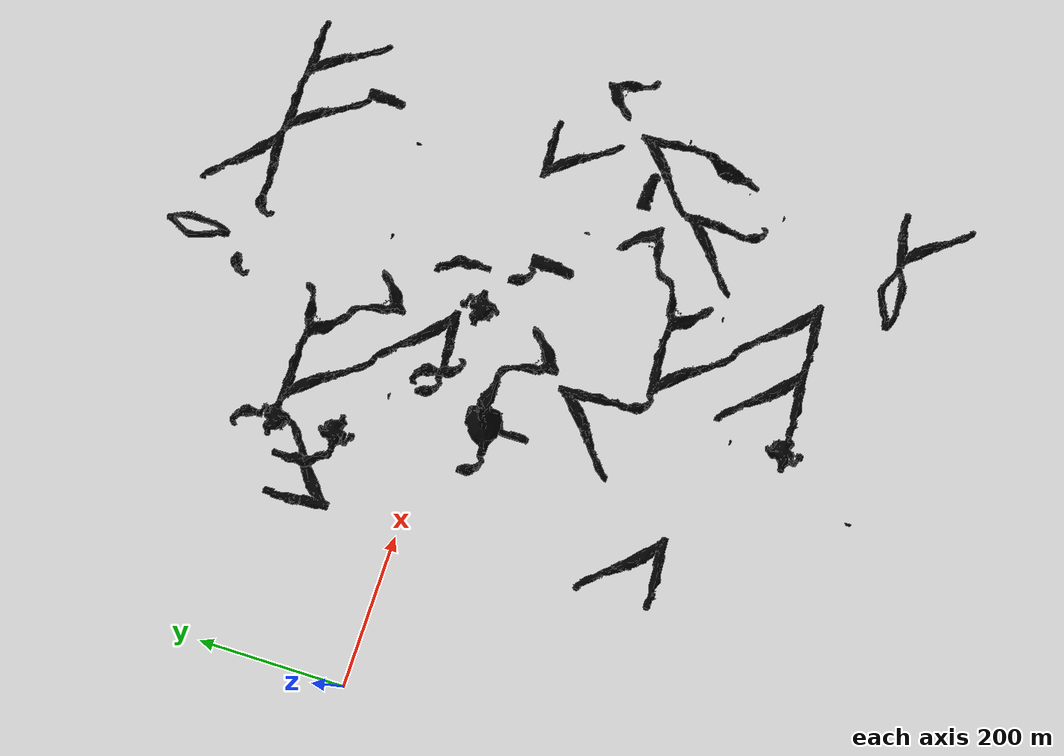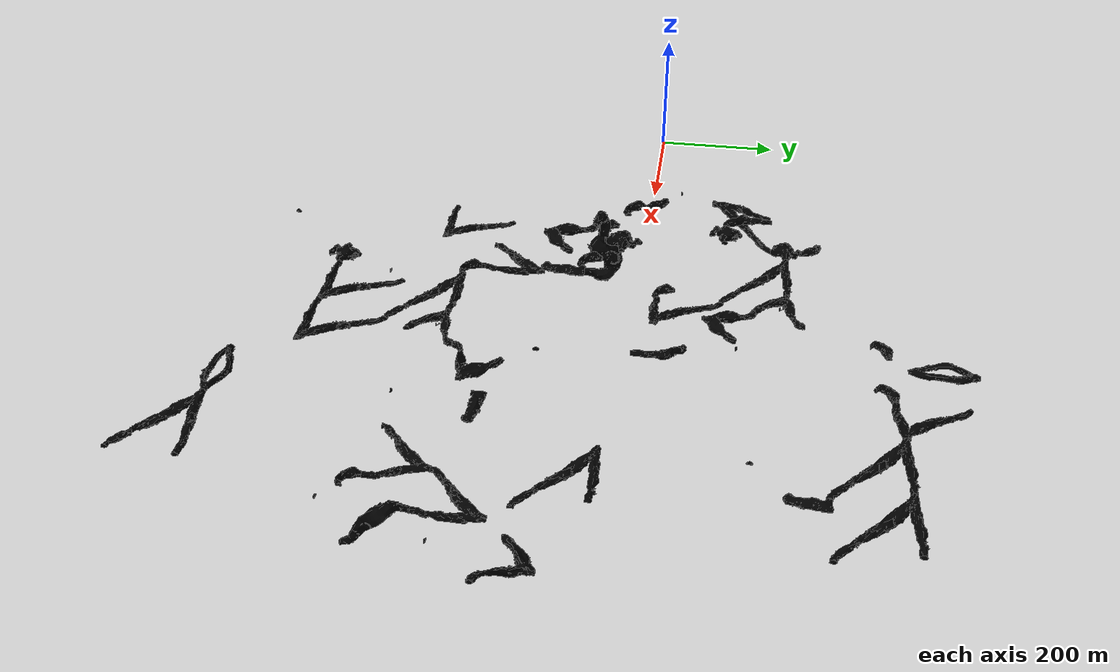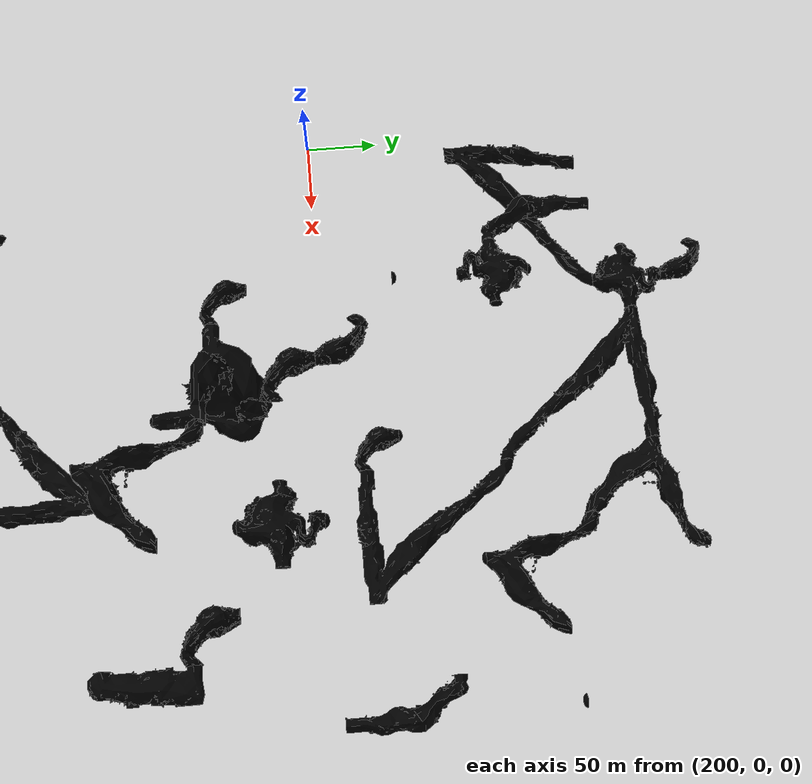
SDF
<sdf version="1.6">
 <world name="cave_circuit_practice_02">
  <plugin name="ros_interface_plugin" filename="librotors_gazebo_ros_interface_plugin.so"/>
  <physics name="1ms" type="ode">
   <max_step_size>0.004</max_step_size>
   <real_time_factor>1.0</real_time_factor>
  </physics>
  <scene>
   <ambient>150 150 150 255</ambient>
   <background>250 250 250 255</background>
   <grid>true</grid>
   <origin_visual>true</origin_visual>
  </scene>
  <include>
   <name>tile_2</name>
   <pose>387.5 -75.0 0.0 0.0 0.0 -1.5708</pose>
   <uri>model://Cave 3 Way Elevation 03 Type A</uri>
  </include>
  <include>
   <name>tile_3</name>
   <pose>312.5 225.0 -25.0 0.0 0.0 0.0</pose>
   <uri>model://Cave 4 Way 01 Lights Type A</uri>
  </include>
  <include>
   <name>tile_4</name>
   <pose>612.5 25.0 -25.0 0.0 0.0 3.14159</pose>
   <uri>model://Cave Corner 02 Type A</uri>
  </include>
  <include>
   <name>tile_9</name>
   <pose>487.5 25.0 -25.0 0.0 0.0 -1.5708</pose>
   <uri>model://Cave 3 Way Elevation 01 Type A</uri>
  </include>
  <include>
   <name>tile_10</name>
   <pose>562.5 450.0 -50.0 0.0 0.0 0.0</pose>
   <uri>model://Cave Split Type A</uri>
  </include>
  <include>
   <name>tile_11</name>
   <pose>212.5 150.0 0.0 0.0 0.0 -3.14159</pose>
   <uri>model://Cave 3 Way Elevation 01 Type A</uri>
  </include>
  <include>
   <name>tile_12</name>
   <pose>312.5 125.0 0.0 0.0 0.0 3.14159</pose>
   <uri>model://Cave 4 Way 01 Lights Type A</uri>
  </include>
  <include>
   <name>tile_15</name>
   <pose>612.5 375.0 -50.0 0.0 0.0 1.57079</pose>
   <uri>model://Cave Corner 03 Type A</uri>
  </include>
  <include>
   <name>tile_17</name>
   <pose>387.5 225.0 -25.0 0.0 0.0 1.5708</pose>
   <uri>model://Cave 3 Way Elevation 02 Lights Type A</uri>
  </include>
  <include>
   <name>tile_20</name>
   <pose>587.5 -100.0 100.0 0.0 0.0 -1.5708</pose>
   <uri>model://Cave 2 Way 01 Type A</uri>
  </include>
  <include>
   <name>tile_21</name>
   <pose>262.5 175.0 0.0 0.0 0.0 0.0</pose>
   <uri>model://Cave Corner 02 Lights Type A</uri>
  </include>
  <include>
   <name>tile_23</name>
   <pose>462.5 225.0 -25.0 0.0 0.0 -1.5708</pose>
   <uri>model://Cave 3 Way 01 Type A</uri>
  </include>
  <include>
   <name>tile_24</name>
   <pose>412.5 25.0 100.0 0.0 0.0 -6.99382e-07</pose>
   <uri>model://Cave Corner 03 Type A</uri>
  </include>
  <include>
   <name>tile_26</name>
   <pose>912.5 -200.0 -75.0 0.0 0.0 0.0</pose>
   <uri>model://Cave 3 Way Elevation 02 Type A</uri>
  </include>
  <include>
   <name>tile_27</name>
   <pose>312.5 275.0 -25.0 0.0 0.0 -1.95505e-06</pose>
   <uri>model://Cave Corner 03 Type A</uri>
  </include>
  <include>
   <name>tile_29</name>
   <pose>837.5 250.0 -50.0 0.0 0.0 -1.5708</pose>
   <uri>model://Cave 2 Way 01 Type A</uri>
  </include>
  <include>
   <name>tile_32</name>
   <pose>512.5 375.0 -50.0 0.0 0.0 1.57079</pose>
   <uri>model://Cave Corner 03 Type A</uri>
  </include>
  <include>
   <name>tile_33</name>
   <pose>462.5 -125.0 75.0 0.0 0.0 0.0</pose>
   <uri>model://Cave 3 Way 01 Type A</uri>
  </include>
  <include>
   <name>tile_36</name>
   <pose>687.5 375.0 -25.0 0.0 0.0 -1.5708</pose>
   <uri>model://Cave 3 Way Elevation 01 Type A</uri>
  </include>
  <include>
   <name>tile_37</name>
   <pose>837.5 -25.0 -50.0 0.0 0.0 1.5708</pose>
   <uri>model://Cave 3 Way Elevation 02 Type A</uri>
  </include>
  <include>
   <name>tile_38</name>
   <pose>987.5 -100.0 -75.0 0.0 0.0 3.14159</pose>
   <uri>model://Cave 3 Way 01 Type A</uri>
  </include>
  <include>
   <name>tile_40</name>
   <pose>412.5 -25.0 100.0 0.0 0.0 3.14159</pose>
   <uri>model://Cave Corner 03 Type A</uri>
  </include>
  <include>
   <name>tile_41</name>
   <pose>562.5 -75.0 100.0 0.0 0.0 3.14159</pose>
   <uri>model://Cave Corner 03 Type A</uri>
  </include>
  <include>
   <name>tile_44</name>
   <pose>812.5 -300.0 -100.0 0.0 0.0 -1.74846e-07</pose>
   <uri>model://Cave 3 Way Elevation 01 Type A</uri>
  </include>
  <include>
   <name>tile_45</name>
   <pose>912.5 -300.0 -150.0 0.0 0.0 -1.5708</pose>
   <uri>model://Cave Elevation 02 Type A</uri>
  </include>
  <include>
   <name>tile_47</name>
   <pose>462.5 -200.0 0.0 0.0 0.0 0.0</pose>
   <uri>model://Cave 3 Way Elevation 02 Lights Type A</uri>
  </include>
  <include>
   <name>tile_48</name>
   <pose>787.5 375.0 -25.0 0.0 0.0 1.5708</pose>
   <uri>model://Cave 3 Way Elevation 02 Type A</uri>
  </include>
  <include>
   <name>tile_49</name>
   <pose>512.5 125.0 -25.0 0.0 0.0 -1.74846e-07</pose>
   <uri>model://Cave 3 Way 01 Type A</uri>
  </include>
  <include>
   <name>tile_51</name>
   <pose>512.5 -25.0 100.0 0.0 0.0 -1.74846e-07</pose>
   <uri>model://Cave 4 Way 01 Lights Type A</uri>
  </include>
  <include>
   <name>tile_52</name>
   <pose>887.5 375.0 -25.0 0.0 0.0 1.5708</pose>
   <uri>model://Cave 3 Way Elevation 02 Type A</uri>
  </include>
  <include>
   <name>tile_53</name>
   <pose>537.5 -275.0 0.0 0.0 0.0 1.5708</pose>
   <uri>model://Cave 3 Way Elevation 02 Type A</uri>
  </include>
  <include>
   <name>tile_54</name>
   <pose>462.5 -275.0 0.0 0.0 0.0 3.14159</pose>
   <uri>model://Cave Corner 03 Type A</uri>
  </include>
  <include>
   <name>tile_56</name>
   <pose>262.5 -350.0 -50.0 0.0 0.0 -1.5708</pose>
   <uri>model://Cave 3 Way Elevation 02 Lights Type A</uri>
  </include>
  <include>
   <name>tile_57</name>
   <pose>637.5 -475.0 0.0 0.0 0.0 -1.5708</pose>
   <uri>model://Cave 3 Way Elevation 02 Type A</uri>
  </include>
  <include>
   <name>tile_58</name>
   <pose>612.5 -275.0 0.0 0.0 0.0 -1.5708</pose>
   <uri>model://Cave 3 Way 01 Type A</uri>
  </include>
  <include>
   <name>tile_59</name>
   <pose>712.5 -225.0 0.0 0.0 0.0 1.5708</pose>
   <uri>model://Cave 3 Way 01 Type A</uri>
  </include>
  <include>
   <name>tile_61</name>
   <pose>787.5 -200.0 0.0 0.0 0.0 0.0</pose>
   <uri>model://Cave 2 Way 01 Type A</uri>
  </include>
  <include>
   <name>tile_64</name>
   <pose>537.5 -475.0 0.0 0.0 0.0 -1.5708</pose>
   <uri>model://Cave 3 Way Elevation 02 Type A</uri>
  </include>
  <include>
   <name>tile_66</name>
   <pose>462.5 -475.0 0.0 0.0 0.0 3.14159</pose>
   <uri>model://Cave 4 Way 01 Type A</uri>
  </include>
  <include>
   <name>tile_70</name>
   <pose>312.5 -75.0 0.0 0.0 0.0 3.14159</pose>
   <uri>model://Cave Corner 03 Type A</uri>
  </include>
  <include>
   <name>tile_73</name>
   <pose>812.5 -375.0 -125.0 0.0 0.0 3.14159</pose>
   <uri>model://Cave Corner 03 Type A</uri>
  </include>
  <include>
   <name>tile_75</name>
   <pose>412.5 25.0 -50.0 0.0 0.0 3.14159</pose>
   <uri>model://Cave Corner 03 Type A</uri>
  </include>
  <include>
   <name>tile_76</name>
   <pose>737.5 -575.0 -25.0 0.0 0.0 -1.5708</pose>
   <uri>model://Cave Split Type A</uri>
  </include>
  <include>
   <name>tile_77</name>
   <pose>837.5 -575.0 -25.0 0.0 0.0 1.5708</pose>
   <uri>model://Cave 3 Way Elevation 01 Type A</uri>
  </include>
  <include>
   <name>cap_01</name>
   <pose>287.5 225.0 -25.0 0.0 0.0 1.5708</pose>
   <uri>model://Cave Cap Type A</uri>
  </include>
  <include>
   <name>cap_02</name>
   <pose>787.5 175.0 -50.0 0.0 0.0 1.5708</pose>
   <uri>model://Cave Cap Type A</uri>
  </include>
  <include>
   <name>cap_03</name>
   <pose>937.5 275.0 -50.0 0.0 0.0 -1.5708</pose>
   <uri>model://Cave Cap Type A</uri>
  </include>
  <include>
   <name>cap_04</name>
   <pose>937.5 375.0 -25.0 0.0 0.0 -1.5708</pose>
   <uri>model://Cave Cap Type A</uri>
  </include>
  <include>
   <name>cap_05</name>
   <pose>612.5 350.0 -50.0 0.0 0.0 3.14159</pose>
   <uri>model://Cave Cap Type A</uri>
  </include>
  <include>
   <name>cap_06</name>
   <pose>612.5 150.0 0.0 0.0 0.0 3.14159</pose>
   <uri>model://Cave Cap Type A</uri>
  </include>
  <include>
   <name>cap_07</name>
   <pose>287.5 275.0 -25.0 0.0 0.0 1.5708</pose>
   <uri>model://Cave Cap Type A</uri>
  </include>
  <include>
   <name>cap_08</name>
   <pose>337.5 125.0 0.0 0.0 0.0 -1.5708</pose>
   <uri>model://Cave Cap Type A</uri>
  </include>
  <include>
   <name>cap_09</name>
   <pose>312.5 150.0 0.0 0.0 0.0 -3.49691e-07</pose>
   <uri>model://Cave Cap Type A</uri>
  </include>
  <include>
   <name>cap_10</name>
   <pose>387.5 -125.0 -50.0 0.0 0.0 3.14159</pose>
   <uri>model://Cave Cap Type A</uri>
  </include>
  <include>
   <name>cap_11</name>
   <pose>1012.5 -150.0 -75.0 0.0 0.0 -1.5708</pose>
   <uri>model://Cave Cap Type A</uri>
  </include>
  <include>
   <name>cap_12</name>
   <pose>937.5 -225.0 -100.0 0.0 0.0 3.14159</pose>
   <uri>model://Cave Cap Type A</uri>
  </include>
  <include>
   <name>cap_13</name>
   <pose>912.5 -350.0 -150.0 0.0 0.0 3.14159</pose>
   <uri>model://Cave Cap Type A</uri>
  </include>
  <include>
   <name>cap_14</name>
   <pose>862.5 -400.0 -125.0 0.0 0.0 3.14159</pose>
   <uri>model://Cave Cap Type A</uri>
  </include>
  <include>
   <name>cap_15</name>
   <pose>662.5 -350.0 -100.0 0.0 0.0 0.0</pose>
   <uri>model://Cave Cap Type A</uri>
  </include>
  <include>
   <name>cap_16</name>
   <pose>637.5 -325.0 0.0 0.0 0.0 -1.5708</pose>
   <uri>model://Cave Cap Type A</uri>
  </include>
  <include>
   <name>cap_17</name>
   <pose>462.5 -400.0 -25.0 0.0 0.0 3.14159</pose>
   <uri>model://Cave Cap Type A</uri>
  </include>
  <include>
   <name>cap_18</name>
   <pose>437.5 -475.0 0.0 0.0 0.0 1.57079</pose>
   <uri>model://Cave Cap Type A</uri>
  </include>
  <include>
   <name>cap_19</name>
   <pose>387.5 -575.0 25.0 0.0 0.0 1.57079</pose>
   <uri>model://Cave Cap Type A</uri>
  </include>
  <include>
   <name>cap_20</name>
   <pose>462.5 -450.0 0.0 0.0 0.0 -2.60673e-06</pose>
   <uri>model://Cave Cap Type A</uri>
  </include>
  <include>
   <name>cap_21</name>
   <pose>887.5 -575.0 -50.0 0.0 0.0 -1.5708</pose>
   <uri>model://Cave Cap Type A</uri>
  </include>
  <include>
   <name>cap_22</name>
   <pose>887.5 -675.0 -50.0 0.0 0.0 -1.5708</pose>
   <uri>model://Cave Cap Type A</uri>
  </include>
  <include>
   <name>cap_23</name>
   <pose>212.5 -250.0 -75.0 0.0 0.0 1.57079</pose>
   <uri>model://Cave Cap Type A</uri>
  </include>
  <include>
   <name>cap_24</name>
   <pose>212.5 -350.0 -50.0 0.0 0.0 1.57079</pose>
   <uri>model://Cave Cap Type A</uri>
  </include>
  <include>
   <name>cap_25</name>
   <pose>512.5 -50.0 100.0 0.0 0.0 3.14159</pose>
   <uri>model://Cave Cap Type A</uri>
  </include>
  <include>
   <name>cap_26</name>
   <pose>512.5 0.0 100.0 0.0 0.0 -2.60673e-06</pose>
   <uri>model://Cave Cap Type A</uri>
  </include>
  <include>
   <name>cap_27</name>
   <pose>812.5 -200.0 0.0 0.0 0.0 3.14159</pose>
   <uri>model://Cave Cap Type A</uri>
  </include>
  <include>
   <name>cap_28</name>
   <pose>412.5 50.0 -50.0 0.0 0.0 -3.49691e-07</pose>
   <uri>model://Cave Cap Type A</uri>
  </include>
  <include>
   <name>cap_29</name>
   <pose>362.5 50.0 100.0 0.0 0.0 -3.49691e-07</pose>
   <uri>model://Cave Cap Type A</uri>
  </include>
  <include>
   <name>cap_30</name>
   <pose>687.5 -125.0 25.0 0.0 0.0 -1.5708</pose>
   <uri>model://Cave Cap Type A</uri>
  </include>
  <include>
   <name>cap_31</name>
   <pose>512.5 100.0 -25.0 0.0 0.0 3.14159</pose>
   <uri>model://Cave Cap Type A</uri>
  </include>
  <wind><linear_velocity>0.000000 0.000000 0.000000</linear_velocity></wind>
  <plugin name="ignition::gazebo" filename="dummy">
   <level name="level0">
    <ref>tile_1</ref>
    <pose>37.5 -75 -24.25 0 0 0</pose>
    <geometry><box><size>301.875 1564 531.5</size></box></geometry>
    <buffer>40</buffer>
   </level>
   <level name="level1">
    <ref>tile_19</ref>
    <pose>112.5 -75 -24.25 0 0 0</pose>
    <geometry><box><size>301.875 1564 531.5</size></box></geometry>
    <buffer>40</buffer>
   </level>
   <level name="level2">
    <ref>rescue_randy_4</ref>
    <pose>211.628 -75 -24.25 0 0 0</pose>
    <geometry><box><size>301.875 1564 531.5</size></box></geometry>
    <buffer>40</buffer>
   </level>
   <level name="level3">
    <ref>tile_5</ref>
    <ref>tile_11</ref>
    <ref>cap_23</ref>
    <ref>cap_24</ref>
    <pose>212.5 -75 -24.25 0 0 0</pose>
    <geometry><box><size>301.875 1564 531.5</size></box></geometry>
    <buffer>40</buffer>
   </level>
   <level name="level4">
    <ref>tile_13</ref>
    <ref>tile_21</ref>
    <ref>tile_56</ref>
    <pose>262.5 -75 -24.25 0 0 0</pose>
    <geometry><box><size>301.875 1564 531.5</size></box></geometry>
    <buffer>40</buffer>
   </level>
   <level name="level5">
    <ref>rope_1</ref>
    <pose>269.866 -75 -24.25 0 0 0</pose>
    <geometry><box><size>301.875 1564 531.5</size></box></geometry>
    <buffer>40</buffer>
   </level>
   <level name="level6">
    <ref>cap_01</ref>
    <ref>cap_07</ref>
    <pose>287.5 -75 -24.25 0 0 0</pose>
    <geometry><box><size>301.875 1564 531.5</size></box></geometry>
    <buffer>40</buffer>
   </level>
   <level name="level7">
    <ref>helmet_3</ref>
    <pose>307.67 -75 -24.25 0 0 0</pose>
    <geometry><box><size>301.875 1564 531.5</size></box></geometry>
    <buffer>40</buffer>
   </level>
   <level name="level8">
    <ref>rope_4</ref>
    <pose>309.476 -75 -24.25 0 0 0</pose>
    <geometry><box><size>301.875 1564 531.5</size></box></geometry>
    <buffer>40</buffer>
   </level>
   <level name="level9">
    <ref>tile_3</ref>
    <ref>tile_6</ref>
    <ref>tile_12</ref>
    <ref>tile_27</ref>
    <ref>tile_70</ref>
    <ref>tile_78</ref>
    <ref>tile_79</ref>
    <ref>cap_09</ref>
    <pose>312.5 -75 -24.25 0 0 0</pose>
    <geometry><box><size>301.875 1564 531.5</size></box></geometry>
    <buffer>40</buffer>
   </level>
   <level name="level10">
    <ref>cap_08</ref>
    <pose>337.5 -75 -24.25 0 0 0</pose>
    <geometry><box><size>301.875 1564 531.5</size></box></geometry>
    <buffer>40</buffer>
   </level>
   <level name="level11">
    <ref>phone_2</ref>
    <pose>359.099 -75 -24.25 0 0 0</pose>
    <geometry><box><size>301.875 1564 531.5</size></box></geometry>
    <buffer>40</buffer>
   </level>
   <level name="level12">
    <ref>tile_35</ref>
    <ref>tile_55</ref>
    <ref>cap_29</ref>
    <pose>362.5 -75 -24.25 0 0 0</pose>
    <geometry><box><size>301.875 1564 531.5</size></box></geometry>
    <buffer>40</buffer>
   </level>
   <level name="level13">
    <ref>rope_2</ref>
    <pose>383.981 -75 -24.25 0 0 0</pose>
    <geometry><box><size>301.875 1564 531.5</size></box></geometry>
    <buffer>40</buffer>
   </level>
   <level name="level14">
    <ref>tile_2</ref>
    <ref>tile_17</ref>
    <ref>cap_10</ref>
    <ref>cap_19</ref>
    <pose>387.5 -75 -24.25 0 0 0</pose>
    <geometry><box><size>301.875 1564 531.5</size></box></geometry>
    <buffer>40</buffer>
   </level>
   <level name="level15">
    <ref>tile_24</ref>
    <ref>tile_40</ref>
    <ref>tile_75</ref>
    <ref>cap_28</ref>
    <pose>412.5 -75 -24.25 0 0 0</pose>
    <geometry><box><size>301.875 1564 531.5</size></box></geometry>
    <buffer>40</buffer>
   </level>
   <level name="level16">
    <ref>tile_69</ref>
    <ref>cap_18</ref>
    <pose>437.5 -75 -24.25 0 0 0</pose>
    <geometry><box><size>301.875 1564 531.5</size></box></geometry>
    <buffer>40</buffer>
   </level>
   <level name="level17">
    <ref>tile_23</ref>
    <ref>tile_33</ref>
    <ref>tile_43</ref>
    <ref>tile_47</ref>
    <ref>tile_54</ref>
    <ref>tile_65</ref>
    <ref>tile_66</ref>
    <ref>tile_82</ref>
    <ref>tile_83</ref>
    <ref>tile_84</ref>
    <ref>cap_17</ref>
    <ref>cap_20</ref>
    <pose>462.5 -75 -24.25 0 0 0</pose>
    <geometry><box><size>301.875 1564 531.5</size></box></geometry>
    <buffer>40</buffer>
   </level>
   <level name="level18">
    <ref>helmet_1</ref>
    <pose>478.8 -75 -24.25 0 0 0</pose>
    <geometry><box><size>301.875 1564 531.5</size></box></geometry>
    <buffer>40</buffer>
   </level>
   <level name="level19">
    <ref>tile_9</ref>
    <ref>tile_67</ref>
    <pose>487.5 -75 -24.25 0 0 0</pose>
    <geometry><box><size>301.875 1564 531.5</size></box></geometry>
    <buffer>40</buffer>
   </level>
   <level name="level20">
    <ref>backpack_1</ref>
    <pose>493.388 -75 -24.25 0 0 0</pose>
    <geometry><box><size>301.875 1564 531.5</size></box></geometry>
    <buffer>40</buffer>
   </level>
   <level name="level21">
    <ref>tile_28</ref>
    <ref>tile_32</ref>
    <ref>tile_49</ref>
    <ref>tile_51</ref>
    <ref>tile_68</ref>
    <ref>tile_80</ref>
    <ref>tile_81</ref>
    <ref>cap_25</ref>
    <ref>cap_26</ref>
    <ref>cap_31</ref>
    <pose>512.5 -75 -24.25 0 0 0</pose>
    <geometry><box><size>301.875 1564 531.5</size></box></geometry>
    <buffer>40</buffer>
   </level>
   <level name="level22">
    <ref>backpack_3</ref>
    <pose>531.62 -75 -24.25 0 0 0</pose>
    <geometry><box><size>301.875 1564 531.5</size></box></geometry>
    <buffer>40</buffer>
   </level>
   <level name="level23">
    <ref>tile_53</ref>
    <ref>tile_64</ref>
    <pose>537.5 -75 -24.25 0 0 0</pose>
    <geometry><box><size>301.875 1564 531.5</size></box></geometry>
    <buffer>40</buffer>
   </level>
   <level name="level24">
    <ref>helmet_2</ref>
    <pose>543.09 -75 -24.25 0 0 0</pose>
    <geometry><box><size>301.875 1564 531.5</size></box></geometry>
    <buffer>40</buffer>
   </level>
   <level name="level25">
    <ref>tile_10</ref>
    <ref>tile_16</ref>
    <ref>tile_30</ref>
    <ref>tile_34</ref>
    <ref>tile_39</ref>
    <ref>tile_41</ref>
    <ref>tile_42</ref>
    <pose>562.5 -75 -24.25 0 0 0</pose>
    <geometry><box><size>301.875 1564 531.5</size></box></geometry>
    <buffer>40</buffer>
   </level>
   <level name="level26">
    <ref>phone_1</ref>
    <pose>571.806 -75 -24.25 0 0 0</pose>
    <geometry><box><size>301.875 1564 531.5</size></box></geometry>
    <buffer>40</buffer>
   </level>
   <level name="level27">
    <ref>tile_7</ref>
    <ref>tile_20</ref>
    <pose>587.5 -75 -24.25 0 0 0</pose>
    <geometry><box><size>301.875 1564 531.5</size></box></geometry>
    <buffer>40</buffer>
   </level>
   <level name="level28">
    <ref>helmet_5</ref>
    <pose>589.533 -75 -24.25 0 0 0</pose>
    <geometry><box><size>301.875 1564 531.5</size></box></geometry>
    <buffer>40</buffer>
   </level>
   <level name="level29">
    <ref>rescue_randy_1</ref>
    <pose>600.6 -75 -24.25 0 0 0</pose>
    <geometry><box><size>301.875 1564 531.5</size></box></geometry>
    <buffer>40</buffer>
   </level>
   <level name="level30">
    <ref>tile_4</ref>
    <ref>tile_15</ref>
    <ref>tile_18</ref>
    <ref>tile_50</ref>
    <ref>tile_58</ref>
    <ref>cap_05</ref>
    <ref>cap_06</ref>
    <pose>612.5 -75 -24.25 0 0 0</pose>
    <geometry><box><size>301.875 1564 531.5</size></box></geometry>
    <buffer>40</buffer>
   </level>
   <level name="level31">
    <ref>tile_57</ref>
    <ref>cap_16</ref>
    <pose>637.5 -75 -24.25 0 0 0</pose>
    <geometry><box><size>301.875 1564 531.5</size></box></geometry>
    <buffer>40</buffer>
   </level>
   <level name="level32">
    <ref>rescue_randy_2</ref>
    <pose>662.25 -75 -24.25 0 0 0</pose>
    <geometry><box><size>301.875 1564 531.5</size></box></geometry>
    <buffer>40</buffer>
   </level>
   <level name="level33">
    <ref>rope_3</ref>
    <pose>662.38 -75 -24.25 0 0 0</pose>
    <geometry><box><size>301.875 1564 531.5</size></box></geometry>
    <buffer>40</buffer>
   </level>
   <level name="level34">
    <ref>tile_46</ref>
    <ref>tile_62</ref>
    <ref>tile_72</ref>
    <ref>cap_15</ref>
    <pose>662.5 -75 -24.25 0 0 0</pose>
    <geometry><box><size>301.875 1564 531.5</size></box></geometry>
    <buffer>40</buffer>
   </level>
   <level name="level35">
    <ref>tile_8</ref>
    <ref>tile_36</ref>
    <ref>cap_30</ref>
    <pose>687.5 -75 -24.25 0 0 0</pose>
    <geometry><box><size>301.875 1564 531.5</size></box></geometry>
    <buffer>40</buffer>
   </level>
   <level name="level36">
    <ref>phone_3</ref>
    <pose>687.608 -75 -24.25 0 0 0</pose>
    <geometry><box><size>301.875 1564 531.5</size></box></geometry>
    <buffer>40</buffer>
   </level>
   <level name="level37">
    <ref>tile_59</ref>
    <ref>tile_71</ref>
    <pose>712.5 -75 -24.25 0 0 0</pose>
    <geometry><box><size>301.875 1564 531.5</size></box></geometry>
    <buffer>40</buffer>
   </level>
   <level name="level38">
    <ref>tile_76</ref>
    <pose>737.5 -75 -24.25 0 0 0</pose>
    <geometry><box><size>301.875 1564 531.5</size></box></geometry>
    <buffer>40</buffer>
   </level>
   <level name="level39">
    <ref>tile_60</ref>
    <pose>762.5 -75 -24.25 0 0 0</pose>
    <geometry><box><size>301.875 1564 531.5</size></box></geometry>
    <buffer>40</buffer>
   </level>
   <level name="level40">
    <ref>tile_48</ref>
    <ref>tile_61</ref>
    <ref>cap_02</ref>
    <pose>787.5 -75 -24.25 0 0 0</pose>
    <geometry><box><size>301.875 1564 531.5</size></box></geometry>
    <buffer>40</buffer>
   </level>
   <level name="level41">
    <ref>rescue_randy_3</ref>
    <pose>798.186 -75 -24.25 0 0 0</pose>
    <geometry><box><size>301.875 1564 531.5</size></box></geometry>
    <buffer>40</buffer>
   </level>
   <level name="level42">
    <ref>tile_44</ref>
    <ref>tile_63</ref>
    <ref>tile_73</ref>
    <ref>cap_27</ref>
    <pose>812.5 -75 -24.25 0 0 0</pose>
    <geometry><box><size>301.875 1564 531.5</size></box></geometry>
    <buffer>40</buffer>
   </level>
   <level name="level43">
    <ref>tile_29</ref>
    <ref>tile_37</ref>
    <ref>tile_77</ref>
    <pose>837.5 -75 -24.25 0 0 0</pose>
    <geometry><box><size>301.875 1564 531.5</size></box></geometry>
    <buffer>40</buffer>
   </level>
   <level name="level44">
    <ref>phone_4</ref>
    <pose>857.57 -75 -24.25 0 0 0</pose>
    <geometry><box><size>301.875 1564 531.5</size></box></geometry>
    <buffer>40</buffer>
   </level>
   <level name="level45">
    <ref>tile_74</ref>
    <ref>cap_14</ref>
    <pose>862.5 -75 -24.25 0 0 0</pose>
    <geometry><box><size>301.875 1564 531.5</size></box></geometry>
    <buffer>40</buffer>
   </level>
   <level name="level46">
    <ref>tile_52</ref>
    <ref>cap_21</ref>
    <ref>cap_22</ref>
    <pose>887.5 -75 -24.25 0 0 0</pose>
    <geometry><box><size>301.875 1564 531.5</size></box></geometry>
    <buffer>40</buffer>
   </level>
   <level name="level47">
    <ref>helmet_4</ref>
    <pose>909.645 -75 -24.25 0 0 0</pose>
    <geometry><box><size>301.875 1564 531.5</size></box></geometry>
    <buffer>40</buffer>
   </level>
   <level name="level48">
    <ref>tile_25</ref>
    <ref>tile_26</ref>
    <ref>tile_45</ref>
    <ref>cap_13</ref>
    <pose>912.5 -75 -24.25 0 0 0</pose>
    <geometry><box><size>301.875 1564 531.5</size></box></geometry>
    <buffer>40</buffer>
   </level>
   <level name="level49">
    <ref>backpack_2</ref>
    <pose>934.3 -75 -24.25 0 0 0</pose>
    <geometry><box><size>301.875 1564 531.5</size></box></geometry>
    <buffer>40</buffer>
   </level>
   <level name="level50">
    <ref>tile_14</ref>
    <ref>tile_31</ref>
    <ref>cap_03</ref>
    <ref>cap_04</ref>
    <ref>cap_12</ref>
    <pose>937.5 -75 -24.25 0 0 0</pose>
    <geometry><box><size>301.875 1564 531.5</size></box></geometry>
    <buffer>40</buffer>
   </level>
   <level name="level51">
    <ref>tile_38</ref>
    <pose>987.5 -75 -24.25 0 0 0</pose>
    <geometry><box><size>301.875 1564 531.5</size></box></geometry>
    <buffer>40</buffer>
   </level>
   <level name="level52">
    <ref>cap_11</ref>
    <pose>1012.5 -75 -24.25 0 0 0</pose>
    <geometry><box><size>301.875 1564 531.5</size></box></geometry>
    <buffer>40</buffer>
   </level>
   <level name="level53">
    <ref>cap_22</ref>
    <pose>525 -675 -24.25 0 0 0</pose>
    <geometry><box><size>1297 341.25 531.5</size></box></geometry>
    <buffer>40</buffer>
   </level>
   <level name="level54">
    <ref>rescue_randy_3</ref>
    <pose>525 -582.511 -24.25 0 0 0</pose>
    <geometry><box><size>1297 341.25 531.5</size></box></geometry>
    <buffer>40</buffer>
   </level>
   <level name="level55">
    <ref>backpack_1</ref>
    <pose>525 -577.02 -24.25 0 0 0</pose>
    <geometry><box><size>1297 341.25 531.5</size></box></geometry>
    <buffer>40</buffer>
   </level>
   <level name="level56">
    <ref>tile_68</ref>
    <ref>tile_69</ref>
    <ref>tile_76</ref>
    <ref>tile_77</ref>
    <ref>cap_19</ref>
    <ref>cap_21</ref>
    <pose>525 -575 -24.25 0 0 0</pose>
    <geometry><box><size>1297 341.25 531.5</size></box></geometry>
    <buffer>40</buffer>
   </level>
   <level name="level57">
    <ref>tile_67</ref>
    <ref>tile_72</ref>
    <pose>525 -525 -24.25 0 0 0</pose>
    <geometry><box><size>1297 341.25 531.5</size></box></geometry>
    <buffer>40</buffer>
   </level>
   <level name="level58">
    <ref>tile_71</ref>
    <pose>525 -500 -24.25 0 0 0</pose>
    <geometry><box><size>1297 341.25 531.5</size></box></geometry>
    <buffer>40</buffer>
   </level>
   <level name="level59">
    <ref>tile_57</ref>
    <ref>tile_64</ref>
    <ref>tile_66</ref>
    <ref>cap_18</ref>
    <pose>525 -475 -24.25 0 0 0</pose>
    <geometry><box><size>1297 341.25 531.5</size></box></geometry>
    <buffer>40</buffer>
   </level>
   <level name="level60">
    <ref>cap_20</ref>
    <pose>525 -450 -24.25 0 0 0</pose>
    <geometry><box><size>1297 341.25 531.5</size></box></geometry>
    <buffer>40</buffer>
   </level>
   <level name="level61">
    <ref>helmet_2</ref>
    <pose>525 -439.504 -24.25 0 0 0</pose>
    <geometry><box><size>1297 341.25 531.5</size></box></geometry>
    <buffer>40</buffer>
   </level>
   <level name="level62">
    <ref>cap_14</ref>
    <ref>cap_17</ref>
    <pose>525 -400 -24.25 0 0 0</pose>
    <geometry><box><size>1297 341.25 531.5</size></box></geometry>
    <buffer>40</buffer>
   </level>
   <level name="level63">
    <ref>tile_46</ref>
    <ref>tile_65</ref>
    <ref>tile_73</ref>
    <ref>tile_74</ref>
    <pose>525 -375 -24.25 0 0 0</pose>
    <geometry><box><size>1297 341.25 531.5</size></box></geometry>
    <buffer>40</buffer>
   </level>
   <level name="level64">
    <ref>phone_3</ref>
    <pose>525 -366.807 -24.25 0 0 0</pose>
    <geometry><box><size>1297 341.25 531.5</size></box></geometry>
    <buffer>40</buffer>
   </level>
   <level name="level65">
    <ref>rope_1</ref>
    <pose>525 -352.272 -24.25 0 0 0</pose>
    <geometry><box><size>1297 341.25 531.5</size></box></geometry>
    <buffer>40</buffer>
   </level>
   <level name="level66">
    <ref>tile_56</ref>
    <ref>cap_13</ref>
    <ref>cap_15</ref>
    <ref>cap_24</ref>
    <pose>525 -350 -24.25 0 0 0</pose>
    <geometry><box><size>1297 341.25 531.5</size></box></geometry>
    <buffer>40</buffer>
   </level>
   <level name="level67">
    <ref>cap_16</ref>
    <pose>525 -325 -24.25 0 0 0</pose>
    <geometry><box><size>1297 341.25 531.5</size></box></geometry>
    <buffer>40</buffer>
   </level>
   <level name="level68">
    <ref>helmet_4</ref>
    <pose>525 -301.683 -24.25 0 0 0</pose>
    <geometry><box><size>1297 341.25 531.5</size></box></geometry>
    <buffer>40</buffer>
   </level>
   <level name="level69">
    <ref>tile_44</ref>
    <ref>tile_45</ref>
    <ref>tile_55</ref>
    <pose>525 -300 -24.25 0 0 0</pose>
    <geometry><box><size>1297 341.25 531.5</size></box></geometry>
    <buffer>40</buffer>
   </level>
   <level name="level70">
    <ref>tile_53</ref>
    <ref>tile_54</ref>
    <ref>tile_58</ref>
    <ref>tile_82</ref>
    <pose>525 -275 -24.25 0 0 0</pose>
    <geometry><box><size>1297 341.25 531.5</size></box></geometry>
    <buffer>40</buffer>
   </level>
   <level name="level71">
    <ref>cap_23</ref>
    <pose>525 -250 -24.25 0 0 0</pose>
    <geometry><box><size>1297 341.25 531.5</size></box></geometry>
    <buffer>40</buffer>
   </level>
   <level name="level72">
    <ref>tile_59</ref>
    <ref>tile_60</ref>
    <ref>tile_83</ref>
    <ref>cap_12</ref>
    <pose>525 -225 -24.25 0 0 0</pose>
    <geometry><box><size>1297 341.25 531.5</size></box></geometry>
    <buffer>40</buffer>
   </level>
   <level name="level73">
    <ref>tile_26</ref>
    <ref>tile_47</ref>
    <ref>tile_61</ref>
    <ref>tile_81</ref>
    <ref>cap_27</ref>
    <pose>525 -200 -24.25 0 0 0</pose>
    <geometry><box><size>1297 341.25 531.5</size></box></geometry>
    <buffer>40</buffer>
   </level>
   <level name="level74">
    <ref>tile_14</ref>
    <ref>tile_84</ref>
    <pose>525 -175 -24.25 0 0 0</pose>
    <geometry><box><size>1297 341.25 531.5</size></box></geometry>
    <buffer>40</buffer>
   </level>
   <level name="level75">
    <ref>cap_11</ref>
    <pose>525 -150 -24.25 0 0 0</pose>
    <geometry><box><size>1297 341.25 531.5</size></box></geometry>
    <buffer>40</buffer>
   </level>
   <level name="level76">
    <ref>rescue_randy_2</ref>
    <pose>525 -136.91 -24.25 0 0 0</pose>
    <geometry><box><size>1297 341.25 531.5</size></box></geometry>
    <buffer>40</buffer>
   </level>
   <level name="level77">
    <ref>helmet_1</ref>
    <pose>525 -129.4 -24.25 0 0 0</pose>
    <geometry><box><size>1297 341.25 531.5</size></box></geometry>
    <buffer>40</buffer>
   </level>
   <level name="level78">
    <ref>tile_25</ref>
    <ref>tile_33</ref>
    <ref>tile_39</ref>
    <ref>tile_62</ref>
    <ref>tile_80</ref>
    <ref>cap_10</ref>
    <ref>cap_30</ref>
    <pose>525 -125 -24.25 0 0 0</pose>
    <geometry><box><size>1297 341.25 531.5</size></box></geometry>
    <buffer>40</buffer>
   </level>
   <level name="level79">
    <ref>tile_20</ref>
    <ref>tile_38</ref>
    <pose>525 -100 -24.25 0 0 0</pose>
    <geometry><box><size>1297 341.25 531.5</size></box></geometry>
    <buffer>40</buffer>
   </level>
   <level name="level80">
    <ref>tile_2</ref>
    <ref>tile_34</ref>
    <ref>tile_41</ref>
    <ref>tile_70</ref>
    <pose>525 -75 -24.25 0 0 0</pose>
    <geometry><box><size>1297 341.25 531.5</size></box></geometry>
    <buffer>40</buffer>
   </level>
   <level name="level81">
    <ref>backpack_3</ref>
    <pose>525 -66.02 -24.25 0 0 0</pose>
    <geometry><box><size>1297 341.25 531.5</size></box></geometry>
    <buffer>40</buffer>
   </level>
   <level name="level82">
    <ref>rope_2</ref>
    <pose>525 -61.3736 -24.25 0 0 0</pose>
    <geometry><box><size>1297 341.25 531.5</size></box></geometry>
    <buffer>40</buffer>
   </level>
   <level name="level83">
    <ref>cap_25</ref>
    <pose>525 -50 -24.25 0 0 0</pose>
    <geometry><box><size>1297 341.25 531.5</size></box></geometry>
    <buffer>40</buffer>
   </level>
   <level name="level84">
    <ref>tile_6</ref>
    <ref>tile_8</ref>
    <ref>tile_31</ref>
    <ref>tile_37</ref>
    <ref>tile_40</ref>
    <ref>tile_42</ref>
    <ref>tile_43</ref>
    <ref>tile_51</ref>
    <pose>525 -25 -24.25 0 0 0</pose>
    <geometry><box><size>1297 341.25 531.5</size></box></geometry>
    <buffer>40</buffer>
   </level>
   <level name="level85">
    <ref>tile_19</ref>
    <pose>525 -1.46484e-05 -24.25 0 0 0</pose>
    <geometry><box><size>1297 341.25 531.5</size></box></geometry>
    <buffer>40</buffer>
   </level>
   <level name="level86">
    <ref>tile_1</ref>
    <ref>cap_26</ref>
    <pose>525 0 -24.25 0 0 0</pose>
    <geometry><box><size>1297 341.25 531.5</size></box></geometry>
    <buffer>40</buffer>
   </level>
   <level name="level87">
    <ref>backpack_2</ref>
    <pose>525 4.95 -24.25 0 0 0</pose>
    <geometry><box><size>1297 341.25 531.5</size></box></geometry>
    <buffer>40</buffer>
   </level>
   <level name="level88">
    <ref>tile_4</ref>
    <ref>tile_9</ref>
    <ref>tile_24</ref>
    <ref>tile_35</ref>
    <ref>tile_75</ref>
    <ref>tile_78</ref>
    <pose>525 25 -24.25 0 0 0</pose>
    <geometry><box><size>1297 341.25 531.5</size></box></geometry>
    <buffer>40</buffer>
   </level>
   <level name="level89">
    <ref>phone_2</ref>
    <pose>525 27.595 -24.25 0 0 0</pose>
    <geometry><box><size>1297 341.25 531.5</size></box></geometry>
    <buffer>40</buffer>
   </level>
   <level name="level90">
    <ref>tile_5</ref>
    <ref>tile_16</ref>
    <ref>cap_28</ref>
    <ref>cap_29</ref>
    <pose>525 50 -24.25 0 0 0</pose>
    <geometry><box><size>1297 341.25 531.5</size></box></geometry>
    <buffer>40</buffer>
   </level>
   <level name="level91">
    <ref>helmet_5</ref>
    <pose>525 74.955 -24.25 0 0 0</pose>
    <geometry><box><size>1297 341.25 531.5</size></box></geometry>
    <buffer>40</buffer>
   </level>
   <level name="level92">
    <ref>tile_79</ref>
    <pose>525 75 -24.25 0 0 0</pose>
    <geometry><box><size>1297 341.25 531.5</size></box></geometry>
    <buffer>40</buffer>
   </level>
   <level name="level93">
    <ref>cap_31</ref>
    <pose>525 100 -24.25 0 0 0</pose>
    <geometry><box><size>1297 341.25 531.5</size></box></geometry>
    <buffer>40</buffer>
   </level>
   <level name="level94">
    <ref>tile_12</ref>
    <ref>tile_49</ref>
    <ref>cap_08</ref>
    <pose>525 125 -24.25 0 0 0</pose>
    <geometry><box><size>1297 341.25 531.5</size></box></geometry>
    <buffer>40</buffer>
   </level>
   <level name="level95">
    <ref>rope_4</ref>
    <pose>525 130.217 -24.25 0 0 0</pose>
    <geometry><box><size>1297 341.25 531.5</size></box></geometry>
    <buffer>40</buffer>
   </level>
   <level name="level96">
    <ref>tile_11</ref>
    <ref>cap_06</ref>
    <ref>cap_09</ref>
    <pose>525 150 -24.25 0 0 0</pose>
    <geometry><box><size>1297 341.25 531.5</size></box></geometry>
    <buffer>40</buffer>
   </level>
   <level name="level97">
    <ref>rescue_randy_4</ref>
    <pose>525 151.321 -24.25 0 0 0</pose>
    <geometry><box><size>1297 341.25 531.5</size></box></geometry>
    <buffer>40</buffer>
   </level>
   <level name="level98">
    <ref>rescue_randy_1</ref>
    <pose>525 170.81 -24.25 0 0 0</pose>
    <geometry><box><size>1297 341.25 531.5</size></box></geometry>
    <buffer>40</buffer>
   </level>
   <level name="level99">
    <ref>tile_21</ref>
    <ref>tile_50</ref>
    <ref>cap_02</ref>
    <pose>525 175 -24.25 0 0 0</pose>
    <geometry><box><size>1297 341.25 531.5</size></box></geometry>
    <buffer>40</buffer>
   </level>
   <level name="level100">
    <ref>tile_63</ref>
    <pose>525 200 -24.25 0 0 0</pose>
    <geometry><box><size>1297 341.25 531.5</size></box></geometry>
    <buffer>40</buffer>
   </level>
   <level name="level101">
    <ref>tile_3</ref>
    <ref>tile_13</ref>
    <ref>tile_17</ref>
    <ref>tile_23</ref>
    <ref>cap_01</ref>
    <pose>525 225 -24.25 0 0 0</pose>
    <geometry><box><size>1297 341.25 531.5</size></box></geometry>
    <buffer>40</buffer>
   </level>
   <level name="level102">
    <ref>tile_29</ref>
    <pose>525 250 -24.25 0 0 0</pose>
    <geometry><box><size>1297 341.25 531.5</size></box></geometry>
    <buffer>40</buffer>
   </level>
   <level name="level103">
    <ref>helmet_3</ref>
    <pose>525 269.271 -24.25 0 0 0</pose>
    <geometry><box><size>1297 341.25 531.5</size></box></geometry>
    <buffer>40</buffer>
   </level>
   <level name="level104">
    <ref>tile_27</ref>
    <ref>cap_03</ref>
    <ref>cap_07</ref>
    <pose>525 275 -24.25 0 0 0</pose>
    <geometry><box><size>1297 341.25 531.5</size></box></geometry>
    <buffer>40</buffer>
   </level>
   <level name="level105">
    <ref>tile_28</ref>
    <pose>525 300 -24.25 0 0 0</pose>
    <geometry><box><size>1297 341.25 531.5</size></box></geometry>
    <buffer>40</buffer>
   </level>
   <level name="level106">
    <ref>cap_05</ref>
    <pose>525 350 -24.25 0 0 0</pose>
    <geometry><box><size>1297 341.25 531.5</size></box></geometry>
    <buffer>40</buffer>
   </level>
   <level name="level107">
    <ref>rope_3</ref>
    <pose>525 370.19 -24.25 0 0 0</pose>
    <geometry><box><size>1297 341.25 531.5</size></box></geometry>
    <buffer>40</buffer>
   </level>
   <level name="level108">
    <ref>phone_4</ref>
    <pose>525 374.985 -24.25 0 0 0</pose>
    <geometry><box><size>1297 341.25 531.5</size></box></geometry>
    <buffer>40</buffer>
   </level>
   <level name="level109">
    <ref>tile_15</ref>
    <ref>tile_30</ref>
    <ref>tile_32</ref>
    <ref>tile_36</ref>
    <ref>tile_48</ref>
    <ref>tile_52</ref>
    <ref>cap_04</ref>
    <pose>525 375 -24.25 0 0 0</pose>
    <geometry><box><size>1297 341.25 531.5</size></box></geometry>
    <buffer>40</buffer>
   </level>
   <level name="level110">
    <ref>tile_10</ref>
    <pose>525 450 -24.25 0 0 0</pose>
    <geometry><box><size>1297 341.25 531.5</size></box></geometry>
    <buffer>40</buffer>
   </level>
   <level name="level111">
    <ref>phone_1</ref>
    <pose>525 452.335 -24.25 0 0 0</pose>
    <geometry><box><size>1297 341.25 531.5</size></box></geometry>
    <buffer>40</buffer>
   </level>
   <level name="level112">
    <ref>tile_18</ref>
    <pose>525 475 -24.25 0 0 0</pose>
    <geometry><box><size>1297 341.25 531.5</size></box></geometry>
    <buffer>40</buffer>
   </level>
   <level name="level113">
    <ref>tile_7</ref>
    <pose>525 525 -24.25 0 0 0</pose>
    <geometry><box><size>1297 341.25 531.5</size></box></geometry>
    <buffer>40</buffer>
   </level>
  </plugin>
 </world>
</sdf>

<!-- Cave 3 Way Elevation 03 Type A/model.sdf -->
<sdf version="1.6">
  <model name="Cave 3 Way Elevation 03 Type A">
    <static>true</static>
    <link name="base_link">
      <collision name="collision">
        <pose>0 0 0 0 0 0</pose>
        <geometry>
          <mesh>
            <uri>model://Cave 3 Way Elevation 03 Type A/meshes/3wayelevation03.dae</uri>
            <scale>1.0 1.0 1.0</scale>
          </mesh>
        </geometry>
      </collision>
      <visual name="Gravel_visual">
        <geometry>
          <mesh>
            <uri>model://Cave 3 Way Elevation 03 Type A/meshes/3wayelevation03.dae</uri>
            <submesh>
              <name>Gravel</name>
              <center>false</center>
            </submesh>
          </mesh>
        </geometry>
        <material>
          <diffuse>0 0 0 1</diffuse>
          <specular>0 0 0 1</specular>
          <pbr>
            <metal>
              <albedo_map>model://Cave 3 Way Elevation 03 Type A/materials/textures/Gravel_Albedo.png</albedo_map>
              <normal_map>model://Cave 3 Way Elevation 03 Type A/materials/textures/Gravel_Normal.png</normal_map>
              <roughness_map>model://Cave 3 Way Elevation 03 Type A/materials/textures/Gravel_Roughness.png</roughness_map>
            </metal>
          </pbr>

          <script>
            <uri>model://Cave 3 Way Elevation 03 Type A/materials/scripts/</uri>
            <uri>model://Cave 3 Way Elevation 03 Type A/materials/textures/</uri>
            <name>CaveTile/Gravel_Diffuse</name>
          </script>
        </material>
      </visual>
      <visual name="StriatedRock_visual">
        <geometry>
          <mesh>
            <uri>model://Cave 3 Way Elevation 03 Type A/meshes/3wayelevation03.dae</uri>
            <submesh>
              <name>StriatedRock</name>
              <center>false</center>
            </submesh>
          </mesh>
        </geometry>
        <material>
          <diffuse>0 0 0 1</diffuse>
          <specular>0 0 0 1</specular>
          <pbr>
            <metal>
              <albedo_map>model://Cave 3 Way Elevation 03 Type A/materials/textures/StriatedRock_Albedo.png</albedo_map>
              <normal_map>model://Cave 3 Way Elevation 03 Type A/materials/textures/StriatedRock_Normal.png</normal_map>
              <roughness_map>model://Cave 3 Way Elevation 03 Type A/materials/textures/StriatedRock_Roughness.png</roughness_map>
            </metal>
          </pbr>

          <script>
            <uri>model://Cave 3 Way Elevation 03 Type A/materials/scripts/</uri>
            <uri>model://Cave 3 Way Elevation 03 Type A/materials/textures/</uri>
            <name>CaveTile/StriatedRock_Diffuse</name>
          </script>
        </material>
      </visual>
      <visual name="RockPile_visual">
        <geometry>
          <mesh>
            <uri>model://Cave 3 Way Elevation 03 Type A/meshes/3wayelevation03.dae</uri>
            <submesh>
              <name>RockPile</name>
              <center>false</center>
            </submesh>
          </mesh>
        </geometry>
        <material>
          <diffuse>0 0 0 1</diffuse>
          <specular>0 0 0 1</specular>
          <pbr>
            <metal>
              <albedo_map>model://Cave 3 Way Elevation 03 Type A/materials/textures/RockPile_Albedo.png</albedo_map>
              <normal_map>model://Cave 3 Way Elevation 03 Type A/materials/textures/RockPile_Normal.png</normal_map>
              <roughness_map>model://Cave 3 Way Elevation 03 Type A/materials/textures/RockPile_Roughness.png</roughness_map>
            </metal>
          </pbr>

          <script>
            <uri>model://Cave 3 Way Elevation 03 Type A/materials/scripts/</uri>
            <uri>model://Cave 3 Way Elevation 03 Type A/materials/textures/</uri>
            <name>CaveTile/RockPile_Diffuse</name>
          </script>
        </material>
      </visual>
      <visual name="CaveWall_visual">
        <geometry>
          <mesh>
            <uri>model://Cave 3 Way Elevation 03 Type A/meshes/3wayelevation03.dae</uri>
            <submesh>
              <name>CaveWall</name>
              <center>false</center>
            </submesh>
          </mesh>
        </geometry>
        <material>
          <diffuse>0 0 0 1</diffuse>
          <specular>0 0 0 1</specular>
          <pbr>
            <metal>
              <albedo_map>model://Cave 3 Way Elevation 03 Type A/materials/textures/CaveWall_Albedo.png</albedo_map>
              <normal_map>model://Cave 3 Way Elevation 03 Type A/materials/textures/CaveWall_Normal.png</normal_map>
              <roughness_map>model://Cave 3 Way Elevation 03 Type A/materials/textures/CaveWall_Roughness.png</roughness_map>
            </metal>
          </pbr>

          <script>
            <uri>model://Cave 3 Way Elevation 03 Type A/materials/scripts/</uri>
            <uri>model://Cave 3 Way Elevation 03 Type A/materials/textures/</uri>
            <name>CaveTile/CaveWall_Diffuse</name>
          </script>
        </material>
      </visual>
    </link>

    <plugin filename="libignition-gazebo-performer-detector-system.so" name="ignition::gazebo::systems::PerformerDetector">
      <topic>/subt_performer_detector</topic>
      <pose>-25 5 -30 0 0 0</pose>
      <header_data>
        <key>type</key>
        <value>vertical</value>
      </header_data>
      <geometry>
        <box>
          <size>25 25 10</size>
        </box>
      </geometry>
    </plugin>

    <plugin filename="libignition-gazebo-performer-detector-system.so" name="ignition::gazebo::systems::PerformerDetector">
      <topic>/subt_performer_detector</topic>
      <pose>-10 5 50 0 0 0</pose>
      <header_data>
        <key>type</key>
        <value>vertical</value>
      </header_data>
      <geometry>
        <box>
          <size>25 25 30</size>
        </box>
      </geometry>
    </plugin>

    <plugin filename="libignition-gazebo-performer-detector-system.so" name="ignition::gazebo::systems::PerformerDetector">
      <topic>/subt_performer_detector</topic>
      <pose>-10 0 0 0 0 0</pose>
      <header_data>
        <key>type</key>
        <value>decision, vertical</value>
      </header_data>
      <geometry>
        <box>
          <size>50 30 30</size>
        </box>
      </geometry>
    </plugin>
  </model>
</sdf>

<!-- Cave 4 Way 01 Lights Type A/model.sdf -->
<sdf version="1.6">
  <model name="Cave 4 Way 01 Lights Type A">
    <static>true</static>
    <include>
      <name>cave_4way_01_type_a</name>
      <uri>model://Cave 4 Way 01 Type A</uri>
    </include>
    <link name="lights">
      <light name="Omni012" type="spot">
        <pose>5.76187 0.0888174 5.11374 0 0 0</pose>
        <attenuation>
          <range>20</range>
          <linear>0.2</linear>
          <constant>1.0</constant>
          <quadratic>0.01</quadratic>
        </attenuation>
        <spot>
          <inner_angle>2.0</inner_angle>
          <outer_angle>3.1</outer_angle>
          <falloff>1.2</falloff>
        </spot>
        <cast_shadows>false</cast_shadows>
      </light>
      <light name="Omni013" type="spot">
        <pose>-11.574 -3.89308 6.40369 0 0 0</pose>
        <diffuse>0 0 0 1</diffuse>
        <specular>0 0 0 1</specular>
        <attenuation>
          <range>20</range>
          <linear>0.2</linear>
          <constant>1.0</constant>
          <quadratic>0.01</quadratic>
        </attenuation>
        <spot>
          <inner_angle>2.0</inner_angle>
          <outer_angle>3.1</outer_angle>
          <falloff>1.2</falloff>
        </spot>
        <cast_shadows>false</cast_shadows>
      </light>
    </link>
  </model>
</sdf>

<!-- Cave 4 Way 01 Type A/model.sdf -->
<sdf version="1.6">
  <model name="Cave 4 Way 01 Type A">
    <static>true</static>
    <link name="base_link">
      <collision name="collision">
        <pose>0 0 0 0 0 0</pose>
        <geometry>
          <mesh>
            <uri>model://Cave 4 Way 01 Type A/meshes/4way01.dae</uri>
            <scale>1.0 1.0 1.0</scale>
          </mesh>
        </geometry>
      </collision>
      <visual name="Gravel_visual">
        <geometry>
          <mesh>
            <uri>model://Cave 4 Way 01 Type A/meshes/4way01.dae</uri>
            <submesh>
              <name>Gravel</name>
              <center>false</center>
            </submesh>
          </mesh>
        </geometry>
        <material>
          <diffuse>0 0 0 1</diffuse>
          <specular>0 0 0 1</specular>
          <pbr>
            <metal>
              <albedo_map>model://Cave 4 Way 01 Type A/materials/textures/Gravel_Albedo.png</albedo_map>
              <normal_map>model://Cave 4 Way 01 Type A/materials/textures/Gravel_Normal.png</normal_map>
              <roughness_map>model://Cave 4 Way 01 Type A/materials/textures/Gravel_Roughness.png</roughness_map>
            </metal>
          </pbr>

          <script>
            <uri>model://Cave 4 Way 01 Type A/materials/scripts/</uri>
            <uri>model://Cave 4 Way 01 Type A/materials/textures/</uri>
            <name>CaveTile/Gravel_Diffuse</name>
          </script>
        </material>
      </visual>
      <visual name="RockPile_visual">
        <geometry>
          <mesh>
            <uri>model://Cave 4 Way 01 Type A/meshes/4way01.dae</uri>
            <submesh>
              <name>RockPile</name>
              <center>false</center>
            </submesh>
          </mesh>
        </geometry>
        <material>
          <diffuse>0 0 0 1</diffuse>
          <specular>0 0 0 1</specular>
          <pbr>
            <metal>
              <albedo_map>model://Cave 4 Way 01 Type A/materials/textures/RockPile_Albedo.png</albedo_map>
              <normal_map>model://Cave 4 Way 01 Type A/materials/textures/RockPile_Normal.png</normal_map>
              <roughness_map>model://Cave 4 Way 01 Type A/materials/textures/RockPile_Roughness.png</roughness_map>
            </metal>
          </pbr>

          <script>
            <uri>model://Cave 4 Way 01 Type A/materials/scripts/</uri>
            <uri>model://Cave 4 Way 01 Type A/materials/textures/</uri>
            <name>CaveTile/RockPile_Diffuse</name>
          </script>
        </material>
      </visual>
      <visual name="StriatedRock_visual">
        <geometry>
          <mesh>
            <uri>model://Cave 4 Way 01 Type A/meshes/4way01.dae</uri>
            <submesh>
              <name>StriatedRock</name>
              <center>false</center>
            </submesh>
          </mesh>
        </geometry>
        <material>
          <diffuse>0 0 0 1</diffuse>
          <specular>0 0 0 1</specular>
          <pbr>
            <metal>
              <albedo_map>model://Cave 4 Way 01 Type A/materials/textures/StriatedRock_Albedo.png</albedo_map>
              <normal_map>model://Cave 4 Way 01 Type A/materials/textures/StriatedRock_Normal.png</normal_map>
              <roughness_map>model://Cave 4 Way 01 Type A/materials/textures/StriatedRock_Roughness.png</roughness_map>
            </metal>
          </pbr>

          <script>
            <uri>model://Cave 4 Way 01 Type A/materials/scripts/</uri>
            <uri>model://Cave 4 Way 01 Type A/materials/textures/</uri>
            <name>CaveTile/StriatedRock_Diffuse</name>
          </script>
        </material>
      </visual>
      <visual name="CaveWall_visual">
        <geometry>
          <mesh>
            <uri>model://Cave 4 Way 01 Type A/meshes/4way01.dae</uri>
            <submesh>
              <name>CaveWall</name>
              <center>false</center>
            </submesh>
          </mesh>
        </geometry>
        <material>
          <diffuse>0 0 0 1</diffuse>
          <specular>0 0 0 1</specular>
          <pbr>
            <metal>
              <albedo_map>model://Cave 4 Way 01 Type A/materials/textures/CaveWall_Albedo.png</albedo_map>
              <normal_map>model://Cave 4 Way 01 Type A/materials/textures/CaveWall_Normal.png</normal_map>
              <roughness_map>model://Cave 4 Way 01 Type A/materials/textures/CaveWall_Roughness.png</roughness_map>
            </metal>
          </pbr>

          <script>
            <uri>model://Cave 4 Way 01 Type A/materials/scripts/</uri>
            <uri>model://Cave 4 Way 01 Type A/materials/textures/</uri>
            <name>CaveTile/CaveWall_Diffuse</name>
          </script>
        </material>
      </visual>
    </link>

    <plugin filename="libignition-gazebo-performer-detector-system.so" name="ignition::gazebo::systems::PerformerDetector">
      <topic>/subt_performer_detector</topic>
      <pose>0 -5 5 0 0 0</pose>
      <header_data>
        <key>type</key>
        <value>decision</value>
      </header_data>
      <geometry>
        <box>
          <size>20 20 12</size>
        </box>
      </geometry>
    </plugin>
  </model>
</sdf>

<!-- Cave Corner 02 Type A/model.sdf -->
<sdf version="1.6">
  <model name="Cave Corner 02 Type A">
    <static>true</static>
    <link name="base_link">
      <collision name="collision">
        <pose>0 0 0 0 0 0</pose>
        <geometry>
          <mesh>
            <uri>model://Cave Corner 02 Type A/meshes/corner02.dae</uri>
            <scale>1.0 1.0 1.0</scale>
          </mesh>
        </geometry>
      </collision>
      <visual name="Gravel_visual">
        <geometry>
          <mesh>
            <uri>model://Cave Corner 02 Type A/meshes/corner02.dae</uri>
            <submesh>
              <name>Gravel</name>
              <center>false</center>
            </submesh>
          </mesh>
        </geometry>
        <material>
          <diffuse>0 0 0 1</diffuse>
          <specular>0 0 0 1</specular>
          <pbr>
            <metal>
              <albedo_map>model://Cave Corner 02 Type A/materials/textures/Gravel_Albedo.png</albedo_map>
              <normal_map>model://Cave Corner 02 Type A/materials/textures/Gravel_Normal.png</normal_map>
              <roughness_map>model://Cave Corner 02 Type A/materials/textures/Gravel_Roughness.png</roughness_map>
            </metal>
          </pbr>

          <script>
            <uri>model://Cave Corner 02 Type A/materials/scripts/</uri>
            <uri>model://Cave Corner 02 Type A/materials/textures/</uri>
            <name>CaveTile/Gravel_Diffuse</name>
          </script>
        </material>
      </visual>
      <visual name="RockPile_visual">
        <geometry>
          <mesh>
            <uri>model://Cave Corner 02 Type A/meshes/corner02.dae</uri>
            <submesh>
              <name>RockPile</name>
              <center>false</center>
            </submesh>
          </mesh>
        </geometry>
        <material>
          <diffuse>0 0 0 1</diffuse>
          <specular>0 0 0 1</specular>
          <pbr>
            <metal>
              <albedo_map>model://Cave Corner 02 Type A/materials/textures/RockPile_Albedo.png</albedo_map>
              <normal_map>model://Cave Corner 02 Type A/materials/textures/RockPile_Normal.png</normal_map>
              <roughness_map>model://Cave Corner 02 Type A/materials/textures/RockPile_Roughness.png</roughness_map>
            </metal>
          </pbr>

          <script>
            <uri>model://Cave Corner 02 Type A/materials/scripts/</uri>
            <uri>model://Cave Corner 02 Type A/materials/textures/</uri>
            <name>CaveTile/RockPile_Diffuse</name>
          </script>
        </material>
      </visual>
      <visual name="StriatedRock_visual">
        <geometry>
          <mesh>
            <uri>model://Cave Corner 02 Type A/meshes/corner02.dae</uri>
            <submesh>
              <name>StriatedRock</name>
              <center>false</center>
            </submesh>
          </mesh>
        </geometry>
        <material>
          <diffuse>0 0 0 1</diffuse>
          <specular>0 0 0 1</specular>
          <pbr>
            <metal>
              <albedo_map>model://Cave Corner 02 Type A/materials/textures/StriatedRock_Albedo.png</albedo_map>
              <normal_map>model://Cave Corner 02 Type A/materials/textures/StriatedRock_Normal.png</normal_map>
              <roughness_map>model://Cave Corner 02 Type A/materials/textures/StriatedRock_Roughness.png</roughness_map>
            </metal>
          </pbr>

          <script>
            <uri>model://Cave Corner 02 Type A/materials/scripts/</uri>
            <uri>model://Cave Corner 02 Type A/materials/textures/</uri>
            <name>CaveTile/StriatedRock_Diffuse</name>
          </script>
        </material>
      </visual>
      <visual name="CaveWall_visual">
        <geometry>
          <mesh>
            <uri>model://Cave Corner 02 Type A/meshes/corner02.dae</uri>
            <submesh>
              <name>CaveWall</name>
              <center>false</center>
            </submesh>
          </mesh>
        </geometry>
        <material>
          <diffuse>0 0 0 1</diffuse>
          <specular>0 0 0 1</specular>
          <pbr>
            <metal>
              <albedo_map>model://Cave Corner 02 Type A/materials/textures/CaveWall_Albedo.png</albedo_map>
              <normal_map>model://Cave Corner 02 Type A/materials/textures/CaveWall_Normal.png</normal_map>
              <roughness_map>model://Cave Corner 02 Type A/materials/textures/CaveWall_Roughness.png</roughness_map>
            </metal>
          </pbr>

          <script>
            <uri>model://Cave Corner 02 Type A/materials/scripts/</uri>
            <uri>model://Cave Corner 02 Type A/materials/textures/</uri>
            <name>CaveTile/CaveWall_Diffuse</name>
          </script>
        </material>
      </visual>
    </link>
  </model>
</sdf>

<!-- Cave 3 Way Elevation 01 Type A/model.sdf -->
<sdf version="1.6">
  <model name="Cave 3 Way Elevation 01 Type A">
    <static>true</static>
    <link name="base_link">
      <collision name="collision">
        <pose>0 0 0 0 0 0</pose>
        <geometry>
          <mesh>
            <uri>model://Cave 3 Way Elevation 01 Type A/meshes/3wayelevation01.dae</uri>
            <scale>1.0 1.0 1.0</scale>
          </mesh>
        </geometry>
      </collision>
      <visual name="CaveWall_visual">
        <geometry>
          <mesh>
            <uri>model://Cave 3 Way Elevation 01 Type A/meshes/3wayelevation01.dae</uri>
            <submesh>
              <name>CaveWall</name>
              <center>false</center>
            </submesh>
          </mesh>
        </geometry>
        <material>
          <diffuse>0 0 0 1</diffuse>
          <specular>0 0 0 1</specular>
          <pbr>
            <metal>
              <albedo_map>model://Cave 3 Way Elevation 01 Type A/materials/textures/CaveWall_Albedo.png</albedo_map>
              <normal_map>model://Cave 3 Way Elevation 01 Type A/materials/textures/CaveWall_Normal.png</normal_map>
              <roughness_map>model://Cave 3 Way Elevation 01 Type A/materials/textures/CaveWall_Roughness.png</roughness_map>
            </metal>
          </pbr>

          <script>
            <uri>model://Cave 3 Way Elevation 01 Type A/materials/scripts/</uri>
            <uri>model://Cave 3 Way Elevation 01 Type A/materials/textures/</uri>
            <name>CaveTile/CaveWall_Diffuse</name>
          </script>
        </material>
      </visual>
      <visual name="Gravel_visual">
        <geometry>
          <mesh>
            <uri>model://Cave 3 Way Elevation 01 Type A/meshes/3wayelevation01.dae</uri>
            <submesh>
              <name>Gravel</name>
              <center>false</center>
            </submesh>
          </mesh>
        </geometry>
        <material>
          <diffuse>0 0 0 1</diffuse>
          <specular>0 0 0 1</specular>
          <pbr>
            <metal>
              <albedo_map>model://Cave 3 Way Elevation 01 Type A/materials/textures/Gravel_Albedo.png</albedo_map>
              <normal_map>model://Cave 3 Way Elevation 01 Type A/materials/textures/Gravel_Normal.png</normal_map>
              <roughness_map>model://Cave 3 Way Elevation 01 Type A/materials/textures/Gravel_Roughness.png</roughness_map>
            </metal>
          </pbr>

          <script>
            <uri>model://Cave 3 Way Elevation 01 Type A/materials/scripts/</uri>
            <uri>model://Cave 3 Way Elevation 01 Type A/materials/textures/</uri>
            <name>CaveTile/Gravel_Diffuse</name>
          </script>
        </material>
      </visual>
      <visual name="StriatedRock_visual">
        <geometry>
          <mesh>
            <uri>model://Cave 3 Way Elevation 01 Type A/meshes/3wayelevation01.dae</uri>
            <submesh>
              <name>StriatedRock</name>
              <center>false</center>
            </submesh>
          </mesh>
        </geometry>
        <material>
          <diffuse>0 0 0 1</diffuse>
          <specular>0 0 0 1</specular>
          <pbr>
            <metal>
              <albedo_map>model://Cave 3 Way Elevation 01 Type A/materials/textures/StriatedRock_Albedo.png</albedo_map>
              <normal_map>model://Cave 3 Way Elevation 01 Type A/materials/textures/StriatedRock_Normal.png</normal_map>
              <roughness_map>model://Cave 3 Way Elevation 01 Type A/materials/textures/StriatedRock_Roughness.png</roughness_map>
            </metal>
          </pbr>

          <script>
            <uri>model://Cave 3 Way Elevation 01 Type A/materials/scripts/</uri>
            <uri>model://Cave 3 Way Elevation 01 Type A/materials/textures/</uri>
            <name>CaveTile/StriatedRock_Diffuse</name>
          </script>
        </material>
      </visual>
      <visual name="RockPile_visual">
        <geometry>
          <mesh>
            <uri>model://Cave 3 Way Elevation 01 Type A/meshes/3wayelevation01.dae</uri>
            <submesh>
              <name>RockPile</name>
              <center>false</center>
            </submesh>
          </mesh>
        </geometry>
        <material>
          <diffuse>0 0 0 1</diffuse>
          <specular>0 0 0 1</specular>
          <pbr>
            <metal>
              <albedo_map>model://Cave 3 Way Elevation 01 Type A/materials/textures/RockPile_Albedo.png</albedo_map>
              <normal_map>model://Cave 3 Way Elevation 01 Type A/materials/textures/RockPile_Normal.png</normal_map>
              <roughness_map>model://Cave 3 Way Elevation 01 Type A/materials/textures/RockPile_Roughness.png</roughness_map>
            </metal>
          </pbr>

          <script>
            <uri>model://Cave 3 Way Elevation 01 Type A/materials/scripts/</uri>
            <uri>model://Cave 3 Way Elevation 01 Type A/materials/textures/</uri>
            <name>CaveTile/RockPile_Diffuse</name>
          </script>
        </material>
      </visual>
    </link>

    <plugin filename="libignition-gazebo-performer-detector-system.so" name="ignition::gazebo::systems::PerformerDetector">
      <topic>/subt_performer_detector</topic>
      <pose>-3.2 42.5 1.7 0 0 0</pose>
      <header_data>
        <key>type</key>
        <value>decision</value>
      </header_data>
      <geometry>
        <box>
          <size>15 15 7</size>
        </box>
      </geometry>
    </plugin>
    <plugin filename="libignition-gazebo-performer-detector-system.so" name="ignition::gazebo::systems::PerformerDetector">
      <topic>/subt_performer_detector</topic>
      <pose>-50 0 -6.5 0 0 0</pose>
      <header_data>
        <key>type</key>
        <value>elevation</value>
      </header_data>
      <geometry>
        <box>
          <size>40 40 20</size>
        </box>
      </geometry>
    </plugin>
  </model>
</sdf>

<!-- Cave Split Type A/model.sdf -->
<sdf version="1.6">
  <model name="Cave Split Type A">
    <static>true</static>
    <link name="base_link">
      <collision name="collision">
        <pose>0 0 0 0 0 0</pose>
        <geometry>
          <mesh>
            <uri>model://Cave Split Type A/meshes/split.dae</uri>
            <scale>1.0 1.0 1.0</scale>
          </mesh>
        </geometry>
      </collision>
      <visual name="Gravel_visual">
        <geometry>
          <mesh>
            <uri>model://Cave Split Type A/meshes/split.dae</uri>
            <submesh>
              <name>Gravel</name>
              <center>false</center>
            </submesh>
          </mesh>
        </geometry>
        <material>
          <diffuse>0 0 0 1</diffuse>
          <specular>0 0 0 1</specular>
          <pbr>
            <metal>
              <albedo_map>model://Cave Split Type A/materials/textures/Gravel_Albedo.png</albedo_map>
              <normal_map>model://Cave Split Type A/materials/textures/Gravel_Normal.png</normal_map>
              <roughness_map>model://Cave Split Type A/materials/textures/Gravel_Roughness.png</roughness_map>
            </metal>
          </pbr>

          <script>
            <uri>model://Cave Split Type A/materials/scripts/</uri>
            <uri>model://Cave Split Type A/materials/textures/</uri>
            <name>CaveTile/Gravel_Diffuse</name>
          </script>
        </material>
      </visual>
      <visual name="RockPile_visual">
        <geometry>
          <mesh>
            <uri>model://Cave Split Type A/meshes/split.dae</uri>
            <submesh>
              <name>RockPile</name>
              <center>false</center>
            </submesh>
          </mesh>
        </geometry>
        <material>
          <diffuse>0 0 0 1</diffuse>
          <specular>0 0 0 1</specular>
          <pbr>
            <metal>
              <albedo_map>model://Cave Split Type A/materials/textures/RockPile_Albedo.png</albedo_map>
              <normal_map>model://Cave Split Type A/materials/textures/RockPile_Normal.png</normal_map>
              <roughness_map>model://Cave Split Type A/materials/textures/RockPile_Roughness.png</roughness_map>
            </metal>
          </pbr>

          <script>
            <uri>model://Cave Split Type A/materials/scripts/</uri>
            <uri>model://Cave Split Type A/materials/textures/</uri>
            <name>CaveTile/RockPile_Diffuse</name>
          </script>
        </material>
      </visual>
      <visual name="StriatedRock_visual">
        <geometry>
          <mesh>
            <uri>model://Cave Split Type A/meshes/split.dae</uri>
            <submesh>
              <name>StriatedRock</name>
              <center>false</center>
            </submesh>
          </mesh>
        </geometry>
        <material>
          <diffuse>0 0 0 1</diffuse>
          <specular>0 0 0 1</specular>
          <pbr>
            <metal>
              <albedo_map>model://Cave Split Type A/materials/textures/StriatedRock_Albedo.png</albedo_map>
              <normal_map>model://Cave Split Type A/materials/textures/StriatedRock_Normal.png</normal_map>
              <roughness_map>model://Cave Split Type A/materials/textures/StriatedRock_Roughness.png</roughness_map>
            </metal>
          </pbr>

          <script>
            <uri>model://Cave Split Type A/materials/scripts/</uri>
            <uri>model://Cave Split Type A/materials/textures/</uri>
            <name>CaveTile/StriatedRock_Diffuse</name>
          </script>
        </material>
      </visual>
      <visual name="CaveWall_visual">
        <geometry>
          <mesh>
            <uri>model://Cave Split Type A/meshes/split.dae</uri>
            <submesh>
              <name>CaveWall</name>
              <center>false</center>
            </submesh>
          </mesh>
        </geometry>
        <material>
          <diffuse>0 0 0 1</diffuse>
          <specular>0 0 0 1</specular>
          <pbr>
            <metal>
              <albedo_map>model://Cave Split Type A/materials/textures/CaveWall_Albedo.png</albedo_map>
              <normal_map>model://Cave Split Type A/materials/textures/CaveWall_Normal.png</normal_map>
              <roughness_map>model://Cave Split Type A/materials/textures/CaveWall_Roughness.png</roughness_map>
            </metal>
          </pbr>

          <script>
            <uri>model://Cave Split Type A/materials/scripts/</uri>
            <uri>model://Cave Split Type A/materials/textures/</uri>
            <name>CaveTile/CaveWall_Diffuse</name>
          </script>
        </material>
      </visual>
    </link>

    <plugin filename="libignition-gazebo-performer-detector-system.so" name="ignition::gazebo::systems::PerformerDetector">
      <topic>/subt_performer_detector</topic>
      <pose>0 -45 5 0 0 0</pose>
      <geometry>
        <box>
          <size>15 15 10</size>
        </box>
      </geometry>
      <header_data>
        <key>type</key>
        <value>decision</value>
      </header_data>
    </plugin>

    <plugin filename="libignition-gazebo-performer-detector-system.so" name="ignition::gazebo::systems::PerformerDetector">
      <topic>/subt_performer_detector</topic>
      <pose>0 45 5 0 0 0</pose>
      <geometry>
        <box>
          <size>15 15 10</size>
        </box>
      </geometry>
      <header_data>
        <key>type</key>
        <value>decision</value>
      </header_data>
    </plugin>
  </model>
</sdf>

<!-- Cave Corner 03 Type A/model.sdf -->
<sdf version="1.6">
  <model name="Cave Corner 03 Type A">
    <static>true</static>
    <link name="base_link">
      <collision name="collision">
        <pose>0 0 0 0 0 0</pose>
        <geometry>
          <mesh>
            <uri>model://Cave Corner 03 Type A/meshes/corner03.dae</uri>
            <scale>1.0 1.0 1.0</scale>
          </mesh>
        </geometry>
      </collision>
      <visual name="CaveWall_visual">
        <geometry>
          <mesh>
            <uri>model://Cave Corner 03 Type A/meshes/corner03.dae</uri>
            <submesh>
              <name>CaveWall</name>
              <center>false</center>
            </submesh>
          </mesh>
        </geometry>
        <material>
          <diffuse>0 0 0 1</diffuse>
          <specular>0 0 0 1</specular>
          <pbr>
            <metal>
              <albedo_map>model://Cave Corner 03 Type A/materials/textures/CaveWall_Albedo.png</albedo_map>
              <normal_map>model://Cave Corner 03 Type A/materials/textures/CaveWall_Normal.png</normal_map>
              <roughness_map>model://Cave Corner 03 Type A/materials/textures/CaveWall_Roughness.png</roughness_map>
            </metal>
          </pbr>

          <script>
            <uri>model://Cave Corner 03 Type A/materials/scripts/</uri>
            <uri>model://Cave Corner 03 Type A/materials/textures/</uri>
            <name>CaveTile/CaveWall_Diffuse</name>
          </script>
        </material>
      </visual>
      <visual name="Gravel_visual">
        <geometry>
          <mesh>
            <uri>model://Cave Corner 03 Type A/meshes/corner03.dae</uri>
            <submesh>
              <name>Gravel</name>
              <center>false</center>
            </submesh>
          </mesh>
        </geometry>
        <material>
          <diffuse>0 0 0 1</diffuse>
          <specular>0 0 0 1</specular>
          <pbr>
            <metal>
              <albedo_map>model://Cave Corner 03 Type A/materials/textures/Gravel_Albedo.png</albedo_map>
              <normal_map>model://Cave Corner 03 Type A/materials/textures/Gravel_Normal.png</normal_map>
              <roughness_map>model://Cave Corner 03 Type A/materials/textures/Gravel_Roughness.png</roughness_map>
            </metal>
          </pbr>

          <script>
            <uri>model://Cave Corner 03 Type A/materials/scripts/</uri>
            <uri>model://Cave Corner 03 Type A/materials/textures/</uri>
            <name>CaveTile/Gravel_Diffuse</name>
          </script>
        </material>
      </visual>
      <visual name="RockPile_visual">
        <geometry>
          <mesh>
            <uri>model://Cave Corner 03 Type A/meshes/corner03.dae</uri>
            <submesh>
              <name>RockPile</name>
              <center>false</center>
            </submesh>
          </mesh>
        </geometry>
        <material>
          <diffuse>0 0 0 1</diffuse>
          <specular>0 0 0 1</specular>
          <pbr>
            <metal>
              <albedo_map>model://Cave Corner 03 Type A/materials/textures/RockPile_Albedo.png</albedo_map>
              <normal_map>model://Cave Corner 03 Type A/materials/textures/RockPile_Normal.png</normal_map>
              <roughness_map>model://Cave Corner 03 Type A/materials/textures/RockPile_Roughness.png</roughness_map>
            </metal>
          </pbr>

          <script>
            <uri>model://Cave Corner 03 Type A/materials/scripts/</uri>
            <uri>model://Cave Corner 03 Type A/materials/textures/</uri>
            <name>CaveTile/RockPile_Diffuse</name>
          </script>
        </material>
      </visual>
      <visual name="StriatedRock_visual">
        <geometry>
          <mesh>
            <uri>model://Cave Corner 03 Type A/meshes/corner03.dae</uri>
            <submesh>
              <name>StriatedRock</name>
              <center>false</center>
            </submesh>
          </mesh>
        </geometry>
        <material>
          <diffuse>0 0 0 1</diffuse>
          <specular>0 0 0 1</specular>
          <pbr>
            <metal>
              <albedo_map>model://Cave Corner 03 Type A/materials/textures/StriatedRock_Albedo.png</albedo_map>
              <normal_map>model://Cave Corner 03 Type A/materials/textures/StriatedRock_Normal.png</normal_map>
              <roughness_map>model://Cave Corner 03 Type A/materials/textures/StriatedRock_Roughness.png</roughness_map>
            </metal>
          </pbr>

          <script>
            <uri>model://Cave Corner 03 Type A/materials/scripts/</uri>
            <uri>model://Cave Corner 03 Type A/materials/textures/</uri>
            <name>CaveTile/StriatedRock_Diffuse</name>
          </script>
        </material>
      </visual>
    </link>
  </model>
</sdf>

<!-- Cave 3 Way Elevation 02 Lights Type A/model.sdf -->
<sdf version="1.6">
  <model name="Cave 3 Way Elevation 02 Lights Type A">
    <include>
      <name>cave_3way_elevation_02_type_a</name>
      <uri>model://Cave 3 Way Elevation 02 Type A</uri>
    </include>
    <static>true</static>
    <link name="lights">
      <light name="Omni001" type="spot">
        <pose>0.875385 36.2999 0.995576 0 0 0</pose>
        <diffuse>0 0 0 1</diffuse>
        <specular>0 0 0 1</specular>
        <attenuation>
          <range>20</range>
          <linear>0.2</linear>
          <constant>1.0</constant>
          <quadratic>0.01</quadratic>
        </attenuation>
        <spot>
          <inner_angle>2.0</inner_angle>
          <outer_angle>3.1</outer_angle>
          <falloff>1.2</falloff>
        </spot>
        <cast_shadows>false</cast_shadows>
      </light>
      <light name="Omni003" type="spot">
        <pose>2.09401 -21.9842 1.79263 0 0 0</pose>
        <diffuse>0 0 0 1</diffuse>
        <specular>0 0 0 1</specular>
        <attenuation>
          <range>20</range>
          <linear>0.2</linear>
          <constant>1.0</constant>
          <quadratic>0.01</quadratic>
        </attenuation>
        <spot>
          <inner_angle>2.0</inner_angle>
          <outer_angle>3.1</outer_angle>
          <falloff>1.2</falloff>
        </spot>
        <cast_shadows>false</cast_shadows>
      </light>
      <light name="Omni005" type="spot">
        <pose>-64.091 -15.0648 -11.9682 0 0 0</pose>
        <diffuse>0 0 0 1</diffuse>
        <specular>0 0 0 1</specular>
        <attenuation>
          <range>20</range>
          <linear>0.2</linear>
          <constant>1.0</constant>
          <quadratic>0.01</quadratic>
        </attenuation>
        <spot>
          <inner_angle>2.0</inner_angle>
          <outer_angle>3.1</outer_angle>
          <falloff>1.2</falloff>
        </spot>
        <cast_shadows>false</cast_shadows>
      </light>
    </link>
  </model>
</sdf>

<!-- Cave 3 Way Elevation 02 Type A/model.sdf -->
<sdf version="1.6">
  <model name="Cave 3 Way Elevation 02 Type A">
    <static>true</static>
    <link name="base_link">
      <collision name="collision">
        <pose>0 0 0 0 0 0</pose>
        <geometry>
          <mesh>
            <uri>model://Cave 3 Way Elevation 02 Type A/meshes/3wayelevation02.dae</uri>
            <scale>1.0 1.0 1.0</scale>
          </mesh>
        </geometry>
      </collision>
      <visual name="CaveWall_visual">
        <geometry>
          <mesh>
            <uri>model://Cave 3 Way Elevation 02 Type A/meshes/3wayelevation02.dae</uri>
            <submesh>
              <name>CaveWall</name>
              <center>false</center>
            </submesh>
          </mesh>
        </geometry>
        <material>
          <diffuse>0 0 0 1</diffuse>
          <specular>0 0 0 1</specular>
          <pbr>
            <metal>
              <albedo_map>model://Cave 3 Way Elevation 02 Type A/materials/textures/CaveWall_Albedo.png</albedo_map>
              <normal_map>model://Cave 3 Way Elevation 02 Type A/materials/textures/CaveWall_Normal.png</normal_map>
              <roughness_map>model://Cave 3 Way Elevation 02 Type A/materials/textures/CaveWall_Roughness.png</roughness_map>
            </metal>
          </pbr>

          <script>
            <uri>model://Cave 3 Way Elevation 02 Type A/materials/scripts/</uri>
            <uri>model://Cave 3 Way Elevation 02 Type A/materials/textures/</uri>
            <name>CaveTile/CaveWall_Diffuse</name>
          </script>
        </material>
      </visual>
      <visual name="Gravel_visual">
        <geometry>
          <mesh>
            <uri>model://Cave 3 Way Elevation 02 Type A/meshes/3wayelevation02.dae</uri>
            <submesh>
              <name>Gravel</name>
              <center>false</center>
            </submesh>
          </mesh>
        </geometry>
        <material>
          <diffuse>0 0 0 1</diffuse>
          <specular>0 0 0 1</specular>
          <pbr>
            <metal>
              <albedo_map>model://Cave 3 Way Elevation 02 Type A/materials/textures/Gravel_Albedo.png</albedo_map>
              <normal_map>model://Cave 3 Way Elevation 02 Type A/materials/textures/Gravel_Normal.png</normal_map>
              <roughness_map>model://Cave 3 Way Elevation 02 Type A/materials/textures/Gravel_Roughness.png</roughness_map>
            </metal>
          </pbr>

          <script>
            <uri>model://Cave 3 Way Elevation 02 Type A/materials/scripts/</uri>
            <uri>model://Cave 3 Way Elevation 02 Type A/materials/textures/</uri>
            <name>CaveTile/Gravel_Diffuse</name>
          </script>
        </material>
      </visual>
      <visual name="StriatedRock_visual">
        <geometry>
          <mesh>
            <uri>model://Cave 3 Way Elevation 02 Type A/meshes/3wayelevation02.dae</uri>
            <submesh>
              <name>StriatedRock</name>
              <center>false</center>
            </submesh>
          </mesh>
        </geometry>
        <material>
          <diffuse>0 0 0 1</diffuse>
          <specular>0 0 0 1</specular>
          <pbr>
            <metal>
              <albedo_map>model://Cave 3 Way Elevation 02 Type A/materials/textures/StriatedRock_Albedo.png</albedo_map>
              <normal_map>model://Cave 3 Way Elevation 02 Type A/materials/textures/StriatedRock_Normal.png</normal_map>
              <roughness_map>model://Cave 3 Way Elevation 02 Type A/materials/textures/StriatedRock_Roughness.png</roughness_map>
            </metal>
          </pbr>

          <script>
            <uri>model://Cave 3 Way Elevation 02 Type A/materials/scripts/</uri>
            <uri>model://Cave 3 Way Elevation 02 Type A/materials/textures/</uri>
            <name>CaveTile/StriatedRock_Diffuse</name>
          </script>
        </material>
      </visual>
      <visual name="RockPile_visual">
        <geometry>
          <mesh>
            <uri>model://Cave 3 Way Elevation 02 Type A/meshes/3wayelevation02.dae</uri>
            <submesh>
              <name>RockPile</name>
              <center>false</center>
            </submesh>
          </mesh>
        </geometry>
        <material>
          <diffuse>0 0 0 1</diffuse>
          <specular>0 0 0 1</specular>
          <pbr>
            <metal>
              <albedo_map>model://Cave 3 Way Elevation 02 Type A/materials/textures/RockPile_Albedo.png</albedo_map>
              <normal_map>model://Cave 3 Way Elevation 02 Type A/materials/textures/RockPile_Normal.png</normal_map>
              <roughness_map>model://Cave 3 Way Elevation 02 Type A/materials/textures/RockPile_Roughness.png</roughness_map>
            </metal>
          </pbr>

          <script>
            <uri>model://Cave 3 Way Elevation 02 Type A/materials/scripts/</uri>
            <uri>model://Cave 3 Way Elevation 02 Type A/materials/textures/</uri>
            <name>CaveTile/RockPile_Diffuse</name>
          </script>
        </material>
      </visual>
    </link>

    <plugin filename="libignition-gazebo-performer-detector-system.so" name="ignition::gazebo::systems::PerformerDetector">
      <topic>/subt_performer_detector</topic>
      <pose>-3.2 42.5 1.7 0 0 0</pose>
      <header_data>
        <key>type</key>
        <value>decision</value>
      </header_data>
      <geometry>
        <box>
          <size>15 15 7</size>
        </box>
      </geometry>
    </plugin>
    <plugin filename="libignition-gazebo-performer-detector-system.so" name="ignition::gazebo::systems::PerformerDetector">
      <topic>/subt_performer_detector</topic>
      <pose>-50 0 -6.5 0 0 0</pose>
      <header_data>
        <key>type</key>
        <value>elevation</value>
      </header_data>
      <geometry>
        <box>
          <size>40 40 20</size>
        </box>
      </geometry>
    </plugin>
  </model>
</sdf>

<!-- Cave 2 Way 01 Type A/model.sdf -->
<sdf version="1.6">
  <model name="Cave 2 Way 01 Type A">
    <static>true</static>
    <link name="base_link">
      <collision name="collision">
        <pose>0 0 0 0 0 0</pose>
        <geometry>
          <mesh>
            <uri>model://Cave 2 Way 01 Type A/meshes/2way01.dae</uri>
            <scale>1.0 1.0 1.0</scale>
          </mesh>
        </geometry>
      </collision>
      <visual name="Gravel_visual">
        <geometry>
          <mesh>
            <uri>model://Cave 2 Way 01 Type A/meshes/2way01.dae</uri>
            <submesh>
              <name>Gravel</name>
              <center>false</center>
            </submesh>
          </mesh>
        </geometry>
        <material>
          <diffuse>0 0 0 1</diffuse>

          <pbr>
            <metal>
              <albedo_map>model://Cave 2 Way 01 Type A/materials/textures/Gravel_Albedo.png</albedo_map>
              <normal_map>model://Cave 2 Way 01 Type A/materials/textures/Gravel_Normal.png</normal_map>
              <roughness_map>model://Cave 2 Way 01 Type A/materials/textures/Gravel_Roughness.png</roughness_map>
            </metal>
          </pbr>

          <script>
            <uri>model://Cave 2 Way 01 Type A/materials/scripts/</uri>
            <uri>model://Cave 2 Way 01 Type A/materials/textures/</uri>
            <name>CaveTile/Gravel_Diffuse</name>
          </script>
        </material>
      </visual>
      <visual name="RockPile_visual">
        <geometry>
          <mesh>
            <uri>model://Cave 2 Way 01 Type A/meshes/2way01.dae</uri>
            <submesh>
              <name>RockPile</name>
              <center>false</center>
            </submesh>
          </mesh>
        </geometry>
        <material>
          <diffuse>0 0 0 1</diffuse>
          <specular>0 0 0 1</specular>
          <pbr>
            <metal>
              <albedo_map>model://Cave 2 Way 01 Type A/materials/textures/RockPile_Albedo.png</albedo_map>
              <normal_map>model://Cave 2 Way 01 Type A/materials/textures/RockPile_Normal.png</normal_map>
              <roughness_map>model://Cave 2 Way 01 Type A/materials/textures/RockPile_Roughness.png</roughness_map>
            </metal>
          </pbr>

          <script>
            <uri>model://Cave 2 Way 01 Type A/materials/scripts/</uri>
            <uri>model://Cave 2 Way 01 Type A/materials/textures/</uri>
            <name>CaveTile/RockPile_Diffuse</name>
          </script>
        </material>
      </visual>
      <visual name="StriatedRock_visual">
        <geometry>
          <mesh>
            <uri>model://Cave 2 Way 01 Type A/meshes/2way01.dae</uri>
            <submesh>
              <name>StriatedRock</name>
              <center>false</center>
            </submesh>
          </mesh>
        </geometry>
        <material>
          <diffuse>0 0 0 1</diffuse>
          <specular>0 0 0 1</specular>
          <pbr>
            <metal>
              <albedo_map>model://Cave 2 Way 01 Type A/materials/textures/StriatedRock_Albedo.png</albedo_map>
              <normal_map>model://Cave 2 Way 01 Type A/materials/textures/StriatedRock_Normal.png</normal_map>
              <roughness_map>model://Cave 2 Way 01 Type A/materials/textures/StriatedRock_Roughness.png</roughness_map>
            </metal>
          </pbr>

          <script>
            <uri>model://Cave 2 Way 01 Type A/materials/scripts/</uri>
            <uri>model://Cave 2 Way 01 Type A/materials/textures/</uri>
            <name>CaveTile/StriatedRock_Diffuse</name>
          </script>
        </material>
      </visual>
      <visual name="CaveWall_visual">
        <geometry>
          <mesh>
            <uri>model://Cave 2 Way 01 Type A/meshes/2way01.dae</uri>
            <submesh>
              <name>CaveWall</name>
              <center>false</center>
            </submesh>
          </mesh>
        </geometry>
        <material>
          <diffuse>0 0 0 1</diffuse>
          <specular>0 0 0 1</specular>
          <pbr>
            <metal>
              <albedo_map>model://Cave 2 Way 01 Type A/materials/textures/CaveWall_Albedo.png</albedo_map>
              <normal_map>model://Cave 2 Way 01 Type A/materials/textures/CaveWall_Normal.png</normal_map>
              <roughness_map>model://Cave 2 Way 01 Type A/materials/textures/CaveWall_Roughness.png</roughness_map>
            </metal>
          </pbr>

          <script>
            <uri>model://Cave 2 Way 01 Type A/materials/scripts/</uri>
            <uri>model://Cave 2 Way 01 Type A/materials/textures/</uri>
            <name>CaveTile/CaveWall_Diffuse</name>
          </script>
        </material>
      </visual>
    </link>
  </model>
</sdf>

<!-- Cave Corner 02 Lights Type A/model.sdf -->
<sdf version="1.6">
  <model name="Cave Corner 02 Lights Type A">
    <include>
      <name>cave_corner_02_type_a</name>
      <uri>model://Cave Corner 02 Type A</uri>
    </include>
    <static>true</static>
    <link name="lights">
      <light name="Omni009" type="spot">
        <pose>5.8147 -29.1165 5.08124 0 0 0</pose>
        <diffuse>0 0 0 1</diffuse>
        <specular>0 0 0 1</specular>
        <attenuation>
          <range>20</range>
          <linear>0.2</linear>
          <constant>1.0</constant>
          <quadratic>0.01</quadratic>
        </attenuation>
        <spot>
          <inner_angle>2.0</inner_angle>
          <outer_angle>3.1</outer_angle>
          <falloff>1.2</falloff>
        </spot>
        <cast_shadows>false</cast_shadows>
      </light>
      <light name="Omni010" type="spot">
        <pose>-1.05491 3.24461 2.89552 0 0 0</pose>
        <diffuse>0 0 0 1</diffuse>
        <specular>0 0 0 1</specular>
        <attenuation>
          <range>20</range>
          <linear>0.2</linear>
          <constant>1.0</constant>
          <quadratic>0.01</quadratic>
        </attenuation>
        <spot>
          <inner_angle>2.0</inner_angle>
          <outer_angle>3.1</outer_angle>
          <falloff>1.2</falloff>
        </spot>
        <cast_shadows>false</cast_shadows>
      </light>
    </link>
  </model>
</sdf>

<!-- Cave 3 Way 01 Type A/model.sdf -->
<sdf version="1.6">
  <model name="Cave 3 Way 01 Type A">
    <static>true</static>
    <link name="base_link">
      <collision name="collision">
        <pose>0 0 0 0 0 0</pose>
        <geometry>
          <mesh>
            <uri>model://Cave 3 Way 01 Type A/meshes/3way01.dae</uri>
            <scale>1.0 1.0 1.0</scale>
          </mesh>
        </geometry>
      </collision>
      <visual name="Gravel_visual">
        <geometry>
          <mesh>
            <uri>model://Cave 3 Way 01 Type A/meshes/3way01.dae</uri>
            <submesh>
              <name>Gravel</name>
              <center>false</center>
            </submesh>
          </mesh>
        </geometry>
        <material>
          <diffuse>0 0 0 1</diffuse>
          <specular>0 0 0 1</specular>
          <pbr>
            <metal>
              <albedo_map>model://Cave 3 Way 01 Type A/materials/textures/Gravel_Albedo.png</albedo_map>
              <normal_map>model://Cave 3 Way 01 Type A/materials/textures/Gravel_Normal.png</normal_map>
              <roughness_map>model://Cave 3 Way 01 Type A/materials/textures/Gravel_Roughness.png</roughness_map>
            </metal>
          </pbr>

          <script>
            <uri>model://Cave 3 Way 01 Type A/materials/scripts/</uri>
            <uri>model://Cave 3 Way 01 Type A/materials/textures/</uri>
            <name>CaveTile/Gravel_Diffuse</name>
          </script>
        </material>
      </visual>
      <visual name="StriatedRock_visual">
        <geometry>
          <mesh>
            <uri>model://Cave 3 Way 01 Type A/meshes/3way01.dae</uri>
            <submesh>
              <name>StriatedRock</name>
              <center>false</center>
            </submesh>
          </mesh>
        </geometry>
        <material>
          <diffuse>0 0 0 1</diffuse>
          <specular>0 0 0 1</specular>
          <pbr>
            <metal>
              <albedo_map>model://Cave 3 Way 01 Type A/materials/textures/StriatedRock_Albedo.png</albedo_map>
              <normal_map>model://Cave 3 Way 01 Type A/materials/textures/StriatedRock_Normal.png</normal_map>
              <roughness_map>model://Cave 3 Way 01 Type A/materials/textures/StriatedRock_Roughness.png</roughness_map>
            </metal>
          </pbr>

          <script>
            <uri>model://Cave 3 Way 01 Type A/materials/scripts/</uri>
            <uri>model://Cave 3 Way 01 Type A/materials/textures/</uri>
            <name>CaveTile/StriatedRock_Diffuse</name>
          </script>
        </material>
      </visual>
      <visual name="RockPile_visual">
        <geometry>
          <mesh>
            <uri>model://Cave 3 Way 01 Type A/meshes/3way01.dae</uri>
            <submesh>
              <name>RockPile</name>
              <center>false</center>
            </submesh>
          </mesh>
        </geometry>
        <material>
          <diffuse>0 0 0 1</diffuse>
          <specular>0 0 0 1</specular>
          <pbr>
            <metal>
              <albedo_map>model://Cave 3 Way 01 Type A/materials/textures/RockPile_Albedo.png</albedo_map>
              <normal_map>model://Cave 3 Way 01 Type A/materials/textures/RockPile_Normal.png</normal_map>
              <roughness_map>model://Cave 3 Way 01 Type A/materials/textures/RockPile_Roughness.png</roughness_map>
            </metal>
          </pbr>

          <script>
            <uri>model://Cave 3 Way 01 Type A/materials/scripts/</uri>
            <uri>model://Cave 3 Way 01 Type A/materials/textures/</uri>
            <name>CaveTile/RockPile_Diffuse</name>
          </script>
        </material>
      </visual>
      <visual name="CaveWall_visual">
        <geometry>
          <mesh>
            <uri>model://Cave 3 Way 01 Type A/meshes/3way01.dae</uri>
            <submesh>
              <name>CaveWall</name>
              <center>false</center>
            </submesh>
          </mesh>
        </geometry>
        <material>
          <diffuse>0 0 0 1</diffuse>
          <specular>0 0 0 1</specular>
          <pbr>
            <metal>
              <albedo_map>model://Cave 3 Way 01 Type A/materials/textures/CaveWall_Albedo.png</albedo_map>
              <normal_map>model://Cave 3 Way 01 Type A/materials/textures/CaveWall_Normal.png</normal_map>
              <roughness_map>model://Cave 3 Way 01 Type A/materials/textures/CaveWall_Roughness.png</roughness_map>
            </metal>
          </pbr>

          <script>
            <uri>model://Cave 3 Way 01 Type A/materials/scripts/</uri>
            <uri>model://Cave 3 Way 01 Type A/materials/textures/</uri>
            <name>CaveTile/CaveWall_Diffuse</name>
          </script>
        </material>
      </visual>
    </link>

    <plugin filename="libignition-gazebo-performer-detector-system.so" name="ignition::gazebo::systems::PerformerDetector">
      <topic>/subt_performer_detector</topic>
      <pose>5 -12 5 0 0 0</pose>
      <header_data>
        <key>type</key>
        <value>decision</value>
      </header_data>
      <geometry>
        <box>
          <size>20 20 15</size>
        </box>
      </geometry>
    </plugin>
  </model>
</sdf>

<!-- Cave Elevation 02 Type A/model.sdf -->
<sdf version="1.6">
  <model name="Cave Elevation 02 Type A">
    <static>true</static>
    <link name="base_link">
      <collision name="collision">
        <pose>0 0 0 0 0 0</pose>
        <geometry>
          <mesh>
            <uri>model://Cave Elevation 02 Type A/meshes/elevation02.dae</uri>
            <scale>1.0 1.0 1.0</scale>
          </mesh>
        </geometry>
      </collision>
      <visual name="Gravel_visual">
        <geometry>
          <mesh>
            <uri>model://Cave Elevation 02 Type A/meshes/elevation02.dae</uri>
            <submesh>
              <name>Gravel</name>
              <center>false</center>
            </submesh>
          </mesh>
        </geometry>
        <material>
          <diffuse>0 0 0 1</diffuse>
          <specular>0 0 0 1</specular>
          <pbr>
            <metal>
              <albedo_map>model://Cave Elevation 02 Type A/materials/textures/Gravel_Albedo.png</albedo_map>
              <normal_map>model://Cave Elevation 02 Type A/materials/textures/Gravel_Normal.png</normal_map>
              <roughness_map>model://Cave Elevation 02 Type A/materials/textures/Gravel_Roughness.png</roughness_map>
            </metal>
          </pbr>

          <script>
            <uri>model://Cave Elevation 02 Type A/materials/scripts/</uri>
            <uri>model://Cave Elevation 02 Type A/materials/textures/</uri>
            <name>CaveTile/Gravel_Diffuse</name>
          </script>
        </material>
      </visual>
      <visual name="RockPile_visual">
        <geometry>
          <mesh>
            <uri>model://Cave Elevation 02 Type A/meshes/elevation02.dae</uri>
            <submesh>
              <name>RockPile</name>
              <center>false</center>
            </submesh>
          </mesh>
        </geometry>
        <material>
          <diffuse>0 0 0 1</diffuse>
          <specular>0 0 0 1</specular>
          <pbr>
            <metal>
              <albedo_map>model://Cave Elevation 02 Type A/materials/textures/RockPile_Albedo.png</albedo_map>
              <normal_map>model://Cave Elevation 02 Type A/materials/textures/RockPile_Normal.png</normal_map>
              <roughness_map>model://Cave Elevation 02 Type A/materials/textures/RockPile_Roughness.png</roughness_map>
            </metal>
          </pbr>

          <script>
            <uri>model://Cave Elevation 02 Type A/materials/scripts/</uri>
            <uri>model://Cave Elevation 02 Type A/materials/textures/</uri>
            <name>CaveTile/RockPile_Diffuse</name>
          </script>
        </material>
      </visual>
      <visual name="StriatedRock_visual">
        <geometry>
          <mesh>
            <uri>model://Cave Elevation 02 Type A/meshes/elevation02.dae</uri>
            <submesh>
              <name>StriatedRock</name>
              <center>false</center>
            </submesh>
          </mesh>
        </geometry>
        <material>
          <diffuse>0 0 0 1</diffuse>
          <specular>0 0 0 1</specular>
          <pbr>
            <metal>
              <albedo_map>model://Cave Elevation 02 Type A/materials/textures/StriatedRock_Albedo.png</albedo_map>
              <normal_map>model://Cave Elevation 02 Type A/materials/textures/StriatedRock_Normal.png</normal_map>
              <roughness_map>model://Cave Elevation 02 Type A/materials/textures/StriatedRock_Roughness.png</roughness_map>
            </metal>
          </pbr>

          <script>
            <uri>model://Cave Elevation 02 Type A/materials/scripts/</uri>
            <uri>model://Cave Elevation 02 Type A/materials/textures/</uri>
            <name>CaveTile/StriatedRock_Diffuse</name>
          </script>
        </material>
      </visual>
      <visual name="CaveWall_visual">
        <geometry>
          <mesh>
            <uri>model://Cave Elevation 02 Type A/meshes/elevation02.dae</uri>
            <submesh>
              <name>CaveWall</name>
              <center>false</center>
            </submesh>
          </mesh>
        </geometry>
        <material>
          <diffuse>0 0 0 1</diffuse>
          <specular>0 0 0 1</specular>
          <pbr>
            <metal>
              <albedo_map>model://Cave Elevation 02 Type A/materials/textures/CaveWall_Albedo.png</albedo_map>
              <normal_map>model://Cave Elevation 02 Type A/materials/textures/CaveWall_Normal.png</normal_map>
              <roughness_map>model://Cave Elevation 02 Type A/materials/textures/CaveWall_Roughness.png</roughness_map>
            </metal>
          </pbr>

          <script>
            <uri>model://Cave Elevation 02 Type A/materials/scripts/</uri>
            <uri>model://Cave Elevation 02 Type A/materials/textures/</uri>
            <name>CaveTile/CaveWall_Diffuse</name>
          </script>
        </material>
      </visual>
    </link>

    <plugin filename="libignition-gazebo-performer-detector-system.so" name="ignition::gazebo::systems::PerformerDetector">
      <header_data>
        <key>type</key>
        <value>vertical</value>
      </header_data>
      <topic>/subt_performer_detector</topic>
      <pose>2.25 -7 42.5 0 0 0</pose>
      <geometry>
        <box>
          <size>58.5 31 81</size>
        </box>
      </geometry>
    </plugin>
  </model>
</sdf>

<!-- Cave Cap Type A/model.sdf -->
<sdf version="1.6">
  <model name="Cave Cap Type A">
    <static>true</static>
    <link name="base_link">
      <collision name="collision">
        <pose>0 0 0 0 0 0</pose>
        <geometry>
          <mesh>
            <uri>model://Cave Cap Type A/meshes/cap.dae</uri>
            <scale>1.0 1.0 1.0</scale>
          </mesh>
        </geometry>
      </collision>
      <visual name="Cave Cap Type A_visual">
        <geometry>
          <mesh>
            <uri>model://Cave Cap Type A/meshes/cap.dae</uri>
          </mesh>
        </geometry>
        <material>
          <diffuse>0 0 0 1</diffuse>
          <specular>0 0 0 1</specular>
          <pbr>
            <metal>
              <albedo_map>model://Cave Cap Type A/materials/textures/CaveWall_Albedo.png</albedo_map>
              <normal_map>model://Cave Cap Type A/materials/textures/CaveWall_Normal.png</normal_map>
              <roughness_map>model://Cave Cap Type A/materials/textures/CaveWall_Roughness.png</roughness_map>
            </metal>
          </pbr>

          <script>
            <uri>model://Cave Cap Type A/materials/scripts/</uri>
            <uri>model://Cave Cap Type A/materials/textures/</uri>
            <name>CaveTile/CaveWall_Diffuse</name>
          </script>
        </material>
      </visual>
    </link>
  </model>
</sdf>
